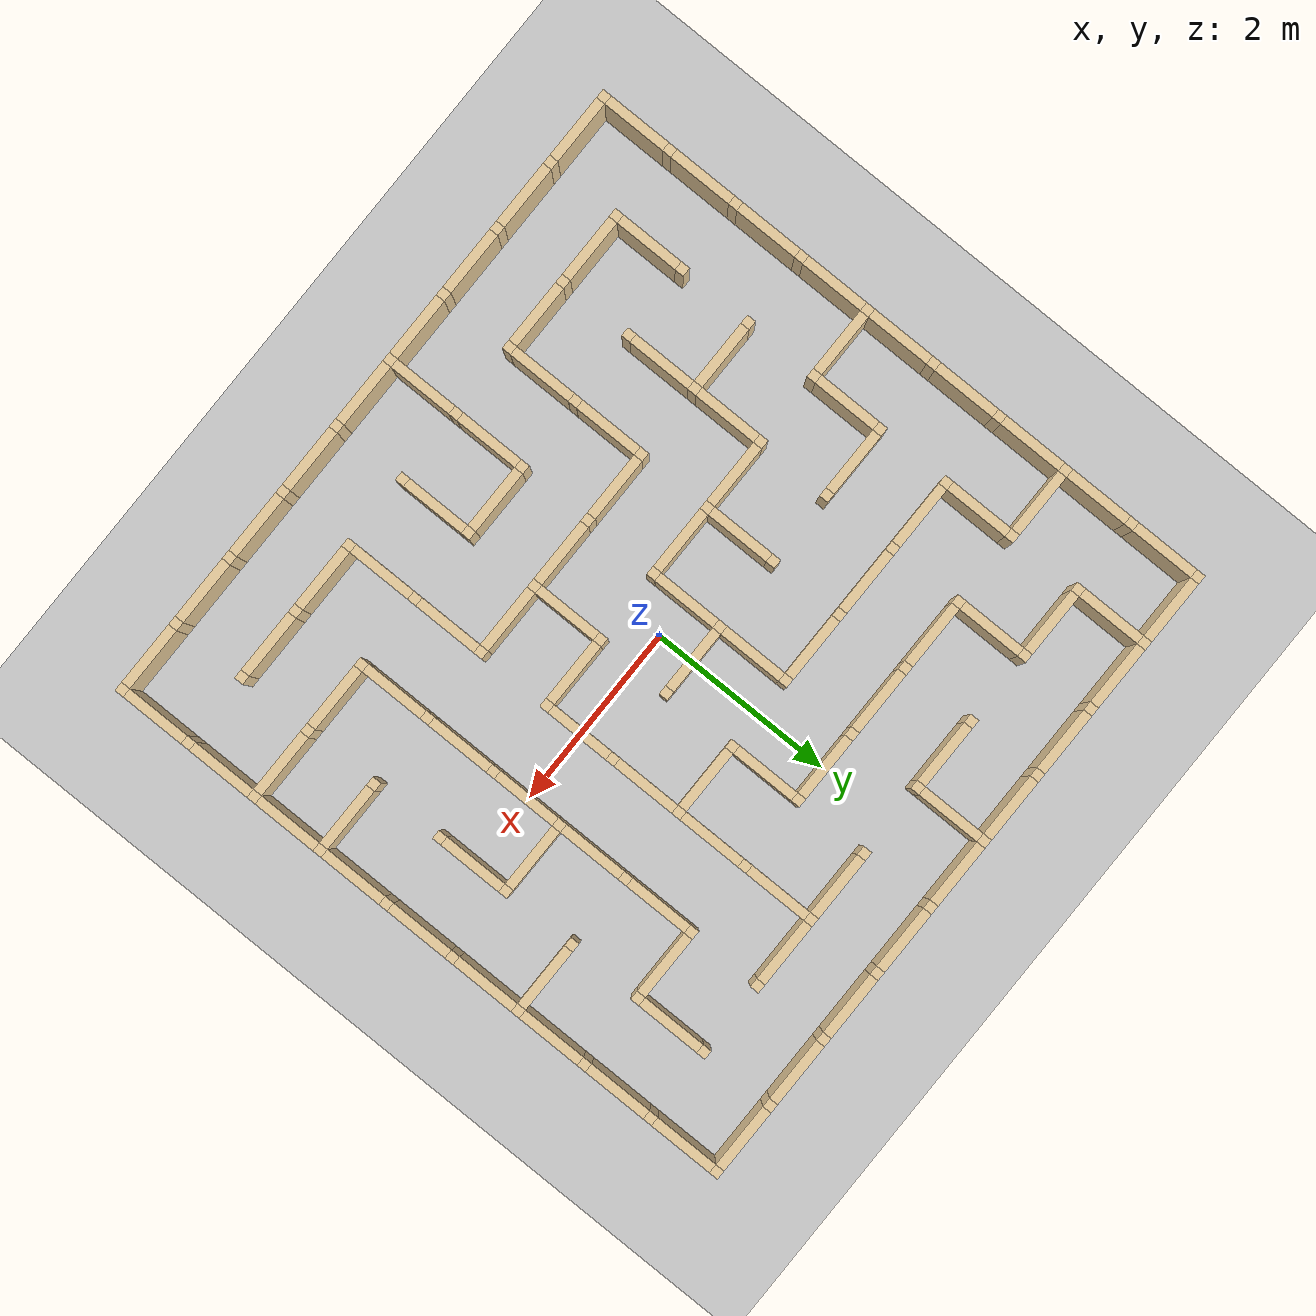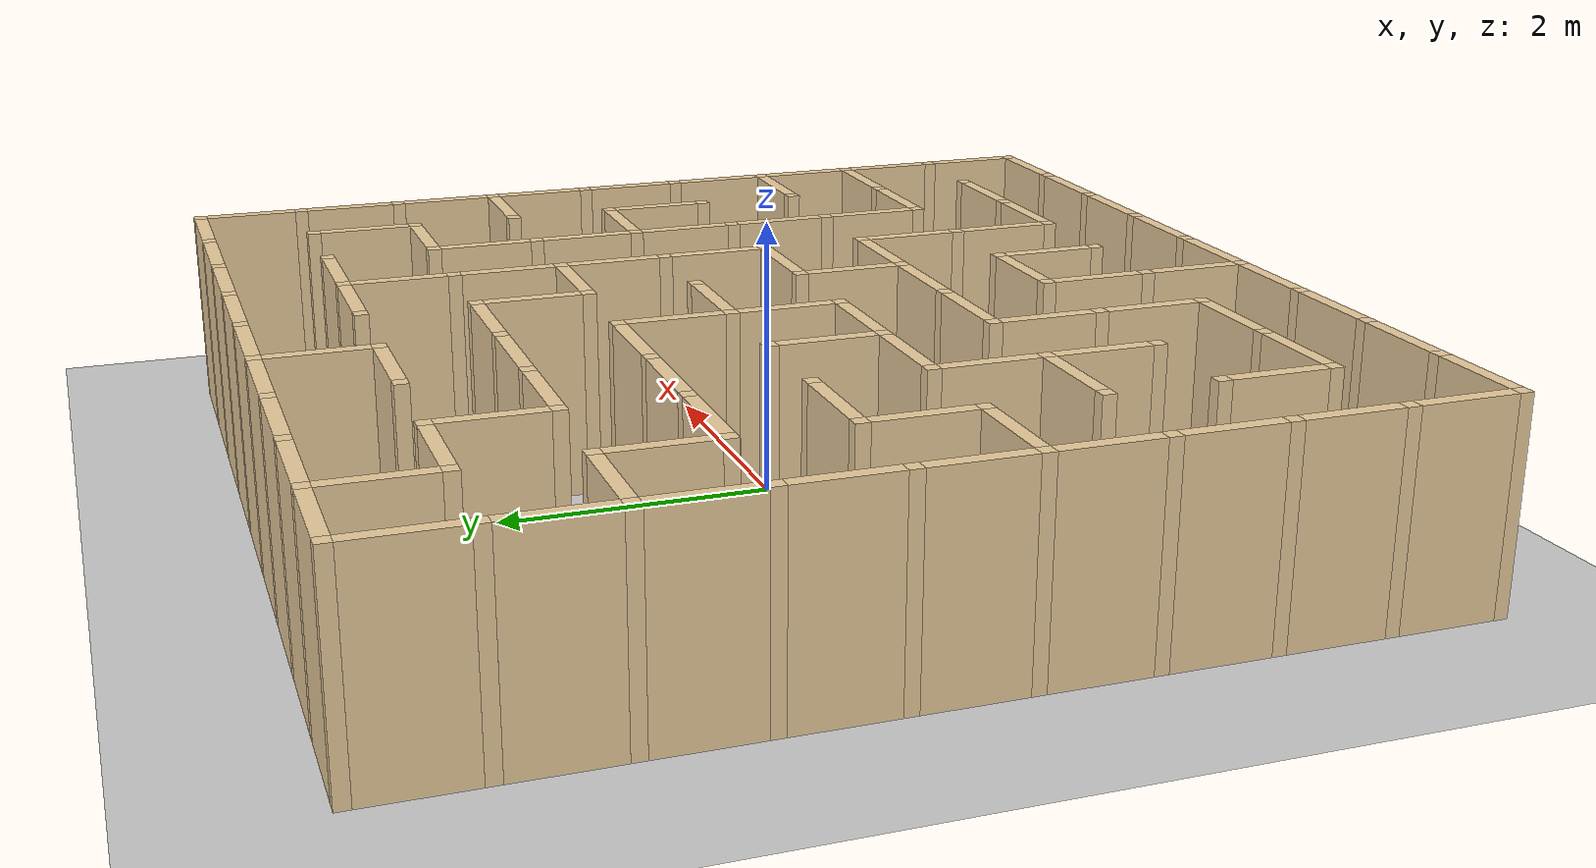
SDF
<?xml version="1.0"?>
<sdf version="1.8">
  <world name="maze_world">

    <plugin
      filename="gz-sim-physics-system"
      name="gz::sim::systems::Physics">
    </plugin>
    <plugin
      filename="gz-sim-user-commands-system"
      name="gz::sim::systems::UserCommands">
    </plugin>
    <plugin
      filename="gz-sim-scene-broadcaster-system"
      name="gz::sim::systems::SceneBroadcaster">
    </plugin>
    <plugin
      filename="gz-sim-sensors-system"
      name="gz::sim::systems::Sensors">
      <render_engine>ogre2</render_engine>
    </plugin>
    <plugin
      filename="gz-sim-imu-system"
      name="gz::sim::systems::Imu">
    </plugin>

    <physics type="ode">
      <real_time_update_rate>1000.0</real_time_update_rate>
      <max_step_size>0.001</max_step_size>
      <real_time_factor>1</real_time_factor>
      <ode>
        <solver>
          <type>quick</type>
          <iters>150</iters>
          <precon_iters>0</precon_iters>
          <sor>1.400000</sor>
          <use_dynamic_moi_rescaling>1</use_dynamic_moi_rescaling>
        </solver>
        <constraints>
          <cfm>0.00001</cfm>
          <erp>0.2</erp>
          <contact_max_correcting_vel>2000.000000</contact_max_correcting_vel>
          <contact_surface_layer>0.01000</contact_surface_layer>
        </constraints>
      </ode>
    </physics>

    <include>
      <uri>https://fuel.gazebosim.org/1.0/OpenRobotics/models/Ground Plane</uri>
    </include>

    <model name="maze">
      <pose>0 0 0 0 0 0</pose>
		  <link name='Wall_0_0_h'>
		    <collision name='Wall_0_Collision'>
		      <geometry>
		        <box>
		          <size>0.7000000000000001 0.1 1.5</size>
		        </box>
		      </geometry>
		      <pose>0 0 0.75 0 -0 0</pose>
		    </collision>
		    <visual name='Wall_0_Visual'>
		      <pose>0 0 0.75 0 -0 0</pose>
		      <geometry>
		        <box>
		          <size>0.7000000000000001 0.1 1.5</size>
		        </box>
		      </geometry>
		      <material>
		        <diffuse>0.921569 0.807843 0.615686 1</diffuse>
		        <ambient>0.921569 0.807843 0.615686 1</ambient>
		      </material>
		      <meta>
		        <layer>0</layer>
		      </meta>
		    </visual>
		    <pose>-3.2 3.6 0 0 -0 0</pose>
		  </link>
        		  <link name='Wall_0_0_v'>
		    <collision name='Wall_0_Collision'>
		      <geometry>
		        <box>
		          <size>0.7000000000000001 0.1 1.5</size>
		        </box>
		      </geometry>
		      <pose>0 0 0.75 0 -0 0</pose>
		    </collision>
		    <visual name='Wall_0_Visual'>
		      <pose>0 0 0.75 0 -0 0</pose>
		      <geometry>
		        <box>
		          <size>0.7000000000000001 0.1 1.5</size>
		        </box>
		      </geometry>
		      <material>
		        <diffuse>0.921569 0.807843 0.615686 1</diffuse>
		        <ambient>0.921569 0.807843 0.615686 1</ambient>
		      </material>
		      <meta>
		        <layer>0</layer>
		      </meta>
		    </visual>
		    <pose>-3.6 3.2 0 0 -0 1.5708</pose>
		  </link>
        	    <link name='Joint_-3.6_3.6'>
		    <collision name='Wall_2_Collision'>
		      <geometry>
		        <box>
		          <size>0.1 0.1 1.5</size>
		        </box>
		      </geometry>
		      <pose>0 0 0.75 0 -0 0</pose>
		    </collision>
		    <visual name='Wall_2_Visual'>
		      <pose>0 0 0.75 0 -0 0</pose>
		      <geometry>
		        <box>
		          <size>0.1 0.1 1.5</size>
		        </box>
		      </geometry>
		      <material>
		        <diffuse>0.921569 0.807843 0.615686 1</diffuse>
		        <ambient>0.721569 0.907843 0.215686 1</ambient>
		      </material>
		      <meta>
		        <layer>0</layer>
		      </meta>
		    </visual>
		    <pose>-3.6 3.6 0 0 -0 0</pose>
		  </link>
        		  <link name='Wall_1_0_h'>
		    <collision name='Wall_0_Collision'>
		      <geometry>
		        <box>
		          <size>0.7000000000000001 0.1 1.5</size>
		        </box>
		      </geometry>
		      <pose>0 0 0.75 0 -0 0</pose>
		    </collision>
		    <visual name='Wall_0_Visual'>
		      <pose>0 0 0.75 0 -0 0</pose>
		      <geometry>
		        <box>
		          <size>0.7000000000000001 0.1 1.5</size>
		        </box>
		      </geometry>
		      <material>
		        <diffuse>0.921569 0.807843 0.615686 1</diffuse>
		        <ambient>0.921569 0.807843 0.615686 1</ambient>
		      </material>
		      <meta>
		        <layer>0</layer>
		      </meta>
		    </visual>
		    <pose>-2.4 3.6 0 0 -0 0</pose>
		  </link>
        		  <link name='Wall_1_0_v'>
		    <collision name='Wall_0_Collision'>
		      <geometry>
		        <box>
		          <size>0.7000000000000001 0.1 1.5</size>
		        </box>
		      </geometry>
		      <pose>0 0 0.75 0 -0 0</pose>
		    </collision>
		    <visual name='Wall_0_Visual'>
		      <pose>0 0 0.75 0 -0 0</pose>
		      <geometry>
		        <box>
		          <size>0.7000000000000001 0.1 1.5</size>
		        </box>
		      </geometry>
		      <material>
		        <diffuse>0.921569 0.807843 0.615686 1</diffuse>
		        <ambient>0.921569 0.807843 0.615686 1</ambient>
		      </material>
		      <meta>
		        <layer>0</layer>
		      </meta>
		    </visual>
		    <pose>-2.8 3.2 0 0 -0 1.5708</pose>
		  </link>
        	    <link name='Joint_-2.8_3.6'>
		    <collision name='Wall_2_Collision'>
		      <geometry>
		        <box>
		          <size>0.1 0.1 1.5</size>
		        </box>
		      </geometry>
		      <pose>0 0 0.75 0 -0 0</pose>
		    </collision>
		    <visual name='Wall_2_Visual'>
		      <pose>0 0 0.75 0 -0 0</pose>
		      <geometry>
		        <box>
		          <size>0.1 0.1 1.5</size>
		        </box>
		      </geometry>
		      <material>
		        <diffuse>0.921569 0.807843 0.615686 1</diffuse>
		        <ambient>0.721569 0.907843 0.215686 1</ambient>
		      </material>
		      <meta>
		        <layer>0</layer>
		      </meta>
		    </visual>
		    <pose>-2.8 3.6 0 0 -0 0</pose>
		  </link>
        		  <link name='Wall_2_0_h'>
		    <collision name='Wall_0_Collision'>
		      <geometry>
		        <box>
		          <size>0.7000000000000001 0.1 1.5</size>
		        </box>
		      </geometry>
		      <pose>0 0 0.75 0 -0 0</pose>
		    </collision>
		    <visual name='Wall_0_Visual'>
		      <pose>0 0 0.75 0 -0 0</pose>
		      <geometry>
		        <box>
		          <size>0.7000000000000001 0.1 1.5</size>
		        </box>
		      </geometry>
		      <material>
		        <diffuse>0.921569 0.807843 0.615686 1</diffuse>
		        <ambient>0.921569 0.807843 0.615686 1</ambient>
		      </material>
		      <meta>
		        <layer>0</layer>
		      </meta>
		    </visual>
		    <pose>-1.6 3.6 0 0 -0 0</pose>
		  </link>
        	    <link name='Joint_-2.0_3.6'>
		    <collision name='Wall_2_Collision'>
		      <geometry>
		        <box>
		          <size>0.1 0.1 1.5</size>
		        </box>
		      </geometry>
		      <pose>0 0 0.75 0 -0 0</pose>
		    </collision>
		    <visual name='Wall_2_Visual'>
		      <pose>0 0 0.75 0 -0 0</pose>
		      <geometry>
		        <box>
		          <size>0.1 0.1 1.5</size>
		        </box>
		      </geometry>
		      <material>
		        <diffuse>0.921569 0.807843 0.615686 1</diffuse>
		        <ambient>0.721569 0.907843 0.215686 1</ambient>
		      </material>
		      <meta>
		        <layer>0</layer>
		      </meta>
		    </visual>
		    <pose>-2.0 3.6 0 0 -0 0</pose>
		  </link>
        		  <link name='Wall_3_0_h'>
		    <collision name='Wall_0_Collision'>
		      <geometry>
		        <box>
		          <size>0.7000000000000001 0.1 1.5</size>
		        </box>
		      </geometry>
		      <pose>0 0 0.75 0 -0 0</pose>
		    </collision>
		    <visual name='Wall_0_Visual'>
		      <pose>0 0 0.75 0 -0 0</pose>
		      <geometry>
		        <box>
		          <size>0.7000000000000001 0.1 1.5</size>
		        </box>
		      </geometry>
		      <material>
		        <diffuse>0.921569 0.807843 0.615686 1</diffuse>
		        <ambient>0.921569 0.807843 0.615686 1</ambient>
		      </material>
		      <meta>
		        <layer>0</layer>
		      </meta>
		    </visual>
		    <pose>-0.7999999999999998 3.6 0 0 -0 0</pose>
		  </link>
        	    <link name='Joint_-1.1999999999999997_3.6'>
		    <collision name='Wall_2_Collision'>
		      <geometry>
		        <box>
		          <size>0.1 0.1 1.5</size>
		        </box>
		      </geometry>
		      <pose>0 0 0.75 0 -0 0</pose>
		    </collision>
		    <visual name='Wall_2_Visual'>
		      <pose>0 0 0.75 0 -0 0</pose>
		      <geometry>
		        <box>
		          <size>0.1 0.1 1.5</size>
		        </box>
		      </geometry>
		      <material>
		        <diffuse>0.921569 0.807843 0.615686 1</diffuse>
		        <ambient>0.721569 0.907843 0.215686 1</ambient>
		      </material>
		      <meta>
		        <layer>0</layer>
		      </meta>
		    </visual>
		    <pose>-1.1999999999999997 3.6 0 0 -0 0</pose>
		  </link>
        		  <link name='Wall_4_0_h'>
		    <collision name='Wall_0_Collision'>
		      <geometry>
		        <box>
		          <size>0.7000000000000001 0.1 1.5</size>
		        </box>
		      </geometry>
		      <pose>0 0 0.75 0 -0 0</pose>
		    </collision>
		    <visual name='Wall_0_Visual'>
		      <pose>0 0 0.75 0 -0 0</pose>
		      <geometry>
		        <box>
		          <size>0.7000000000000001 0.1 1.5</size>
		        </box>
		      </geometry>
		      <material>
		        <diffuse>0.921569 0.807843 0.615686 1</diffuse>
		        <ambient>0.921569 0.807843 0.615686 1</ambient>
		      </material>
		      <meta>
		        <layer>0</layer>
		      </meta>
		    </visual>
		    <pose>0.0 3.6 0 0 -0 0</pose>
		  </link>
        		  <link name='Wall_4_0_v'>
		    <collision name='Wall_0_Collision'>
		      <geometry>
		        <box>
		          <size>0.7000000000000001 0.1 1.5</size>
		        </box>
		      </geometry>
		      <pose>0 0 0.75 0 -0 0</pose>
		    </collision>
		    <visual name='Wall_0_Visual'>
		      <pose>0 0 0.75 0 -0 0</pose>
		      <geometry>
		        <box>
		          <size>0.7000000000000001 0.1 1.5</size>
		        </box>
		      </geometry>
		      <material>
		        <diffuse>0.921569 0.807843 0.615686 1</diffuse>
		        <ambient>0.921569 0.807843 0.615686 1</ambient>
		      </material>
		      <meta>
		        <layer>0</layer>
		      </meta>
		    </visual>
		    <pose>-0.3999999999999999 3.2 0 0 -0 1.5708</pose>
		  </link>
        	    <link name='Joint_-0.3999999999999999_3.6'>
		    <collision name='Wall_2_Collision'>
		      <geometry>
		        <box>
		          <size>0.1 0.1 1.5</size>
		        </box>
		      </geometry>
		      <pose>0 0 0.75 0 -0 0</pose>
		    </collision>
		    <visual name='Wall_2_Visual'>
		      <pose>0 0 0.75 0 -0 0</pose>
		      <geometry>
		        <box>
		          <size>0.1 0.1 1.5</size>
		        </box>
		      </geometry>
		      <material>
		        <diffuse>0.921569 0.807843 0.615686 1</diffuse>
		        <ambient>0.721569 0.907843 0.215686 1</ambient>
		      </material>
		      <meta>
		        <layer>0</layer>
		      </meta>
		    </visual>
		    <pose>-0.3999999999999999 3.6 0 0 -0 0</pose>
		  </link>
        		  <link name='Wall_5_0_h'>
		    <collision name='Wall_0_Collision'>
		      <geometry>
		        <box>
		          <size>0.7000000000000001 0.1 1.5</size>
		        </box>
		      </geometry>
		      <pose>0 0 0.75 0 -0 0</pose>
		    </collision>
		    <visual name='Wall_0_Visual'>
		      <pose>0 0 0.75 0 -0 0</pose>
		      <geometry>
		        <box>
		          <size>0.7000000000000001 0.1 1.5</size>
		        </box>
		      </geometry>
		      <material>
		        <diffuse>0.921569 0.807843 0.615686 1</diffuse>
		        <ambient>0.921569 0.807843 0.615686 1</ambient>
		      </material>
		      <meta>
		        <layer>0</layer>
		      </meta>
		    </visual>
		    <pose>0.8000000000000003 3.6 0 0 -0 0</pose>
		  </link>
        	    <link name='Joint_0.3999999999999999_3.6'>
		    <collision name='Wall_2_Collision'>
		      <geometry>
		        <box>
		          <size>0.1 0.1 1.5</size>
		        </box>
		      </geometry>
		      <pose>0 0 0.75 0 -0 0</pose>
		    </collision>
		    <visual name='Wall_2_Visual'>
		      <pose>0 0 0.75 0 -0 0</pose>
		      <geometry>
		        <box>
		          <size>0.1 0.1 1.5</size>
		        </box>
		      </geometry>
		      <material>
		        <diffuse>0.921569 0.807843 0.615686 1</diffuse>
		        <ambient>0.721569 0.907843 0.215686 1</ambient>
		      </material>
		      <meta>
		        <layer>0</layer>
		      </meta>
		    </visual>
		    <pose>0.3999999999999999 3.6 0 0 -0 0</pose>
		  </link>
        		  <link name='Wall_6_0_h'>
		    <collision name='Wall_0_Collision'>
		      <geometry>
		        <box>
		          <size>0.7000000000000001 0.1 1.5</size>
		        </box>
		      </geometry>
		      <pose>0 0 0.75 0 -0 0</pose>
		    </collision>
		    <visual name='Wall_0_Visual'>
		      <pose>0 0 0.75 0 -0 0</pose>
		      <geometry>
		        <box>
		          <size>0.7000000000000001 0.1 1.5</size>
		        </box>
		      </geometry>
		      <material>
		        <diffuse>0.921569 0.807843 0.615686 1</diffuse>
		        <ambient>0.921569 0.807843 0.615686 1</ambient>
		      </material>
		      <meta>
		        <layer>0</layer>
		      </meta>
		    </visual>
		    <pose>1.600000000000001 3.6 0 0 -0 0</pose>
		  </link>
        	    <link name='Joint_1.2000000000000006_3.6'>
		    <collision name='Wall_2_Collision'>
		      <geometry>
		        <box>
		          <size>0.1 0.1 1.5</size>
		        </box>
		      </geometry>
		      <pose>0 0 0.75 0 -0 0</pose>
		    </collision>
		    <visual name='Wall_2_Visual'>
		      <pose>0 0 0.75 0 -0 0</pose>
		      <geometry>
		        <box>
		          <size>0.1 0.1 1.5</size>
		        </box>
		      </geometry>
		      <material>
		        <diffuse>0.921569 0.807843 0.615686 1</diffuse>
		        <ambient>0.721569 0.907843 0.215686 1</ambient>
		      </material>
		      <meta>
		        <layer>0</layer>
		      </meta>
		    </visual>
		    <pose>1.2000000000000006 3.6 0 0 -0 0</pose>
		  </link>
        		  <link name='Wall_7_0_h'>
		    <collision name='Wall_0_Collision'>
		      <geometry>
		        <box>
		          <size>0.7000000000000001 0.1 1.5</size>
		        </box>
		      </geometry>
		      <pose>0 0 0.75 0 -0 0</pose>
		    </collision>
		    <visual name='Wall_0_Visual'>
		      <pose>0 0 0.75 0 -0 0</pose>
		      <geometry>
		        <box>
		          <size>0.7000000000000001 0.1 1.5</size>
		        </box>
		      </geometry>
		      <material>
		        <diffuse>0.921569 0.807843 0.615686 1</diffuse>
		        <ambient>0.921569 0.807843 0.615686 1</ambient>
		      </material>
		      <meta>
		        <layer>0</layer>
		      </meta>
		    </visual>
		    <pose>2.400000000000001 3.6 0 0 -0 0</pose>
		  </link>
        	    <link name='Joint_2.0000000000000004_3.6'>
		    <collision name='Wall_2_Collision'>
		      <geometry>
		        <box>
		          <size>0.1 0.1 1.5</size>
		        </box>
		      </geometry>
		      <pose>0 0 0.75 0 -0 0</pose>
		    </collision>
		    <visual name='Wall_2_Visual'>
		      <pose>0 0 0.75 0 -0 0</pose>
		      <geometry>
		        <box>
		          <size>0.1 0.1 1.5</size>
		        </box>
		      </geometry>
		      <material>
		        <diffuse>0.921569 0.807843 0.615686 1</diffuse>
		        <ambient>0.721569 0.907843 0.215686 1</ambient>
		      </material>
		      <meta>
		        <layer>0</layer>
		      </meta>
		    </visual>
		    <pose>2.0000000000000004 3.6 0 0 -0 0</pose>
		  </link>
        		  <link name='Wall_8_0_h'>
		    <collision name='Wall_0_Collision'>
		      <geometry>
		        <box>
		          <size>0.7000000000000001 0.1 1.5</size>
		        </box>
		      </geometry>
		      <pose>0 0 0.75 0 -0 0</pose>
		    </collision>
		    <visual name='Wall_0_Visual'>
		      <pose>0 0 0.75 0 -0 0</pose>
		      <geometry>
		        <box>
		          <size>0.7000000000000001 0.1 1.5</size>
		        </box>
		      </geometry>
		      <material>
		        <diffuse>0.921569 0.807843 0.615686 1</diffuse>
		        <ambient>0.921569 0.807843 0.615686 1</ambient>
		      </material>
		      <meta>
		        <layer>0</layer>
		      </meta>
		    </visual>
		    <pose>3.2000000000000006 3.6 0 0 -0 0</pose>
		  </link>
        	    <link name='Joint_2.8000000000000003_3.6'>
		    <collision name='Wall_2_Collision'>
		      <geometry>
		        <box>
		          <size>0.1 0.1 1.5</size>
		        </box>
		      </geometry>
		      <pose>0 0 0.75 0 -0 0</pose>
		    </collision>
		    <visual name='Wall_2_Visual'>
		      <pose>0 0 0.75 0 -0 0</pose>
		      <geometry>
		        <box>
		          <size>0.1 0.1 1.5</size>
		        </box>
		      </geometry>
		      <material>
		        <diffuse>0.921569 0.807843 0.615686 1</diffuse>
		        <ambient>0.721569 0.907843 0.215686 1</ambient>
		      </material>
		      <meta>
		        <layer>0</layer>
		      </meta>
		    </visual>
		    <pose>2.8000000000000003 3.6 0 0 -0 0</pose>
		  </link>
        		  <link name='Wall_9_0_v'>
		    <collision name='Wall_0_Collision'>
		      <geometry>
		        <box>
		          <size>0.7000000000000001 0.1 1.5</size>
		        </box>
		      </geometry>
		      <pose>0 0 0.75 0 -0 0</pose>
		    </collision>
		    <visual name='Wall_0_Visual'>
		      <pose>0 0 0.75 0 -0 0</pose>
		      <geometry>
		        <box>
		          <size>0.7000000000000001 0.1 1.5</size>
		        </box>
		      </geometry>
		      <material>
		        <diffuse>0.921569 0.807843 0.615686 1</diffuse>
		        <ambient>0.921569 0.807843 0.615686 1</ambient>
		      </material>
		      <meta>
		        <layer>0</layer>
		      </meta>
		    </visual>
		    <pose>3.6 3.2 0 0 -0 1.5708</pose>
		  </link>
        	    <link name='Joint_3.6_3.6'>
		    <collision name='Wall_2_Collision'>
		      <geometry>
		        <box>
		          <size>0.1 0.1 1.5</size>
		        </box>
		      </geometry>
		      <pose>0 0 0.75 0 -0 0</pose>
		    </collision>
		    <visual name='Wall_2_Visual'>
		      <pose>0 0 0.75 0 -0 0</pose>
		      <geometry>
		        <box>
		          <size>0.1 0.1 1.5</size>
		        </box>
		      </geometry>
		      <material>
		        <diffuse>0.921569 0.807843 0.615686 1</diffuse>
		        <ambient>0.721569 0.907843 0.215686 1</ambient>
		      </material>
		      <meta>
		        <layer>0</layer>
		      </meta>
		    </visual>
		    <pose>3.6 3.6 0 0 -0 0</pose>
		  </link>
        		  <link name='Wall_0_1_v'>
		    <collision name='Wall_0_Collision'>
		      <geometry>
		        <box>
		          <size>0.7000000000000001 0.1 1.5</size>
		        </box>
		      </geometry>
		      <pose>0 0 0.75 0 -0 0</pose>
		    </collision>
		    <visual name='Wall_0_Visual'>
		      <pose>0 0 0.75 0 -0 0</pose>
		      <geometry>
		        <box>
		          <size>0.7000000000000001 0.1 1.5</size>
		        </box>
		      </geometry>
		      <material>
		        <diffuse>0.921569 0.807843 0.615686 1</diffuse>
		        <ambient>0.921569 0.807843 0.615686 1</ambient>
		      </material>
		      <meta>
		        <layer>0</layer>
		      </meta>
		    </visual>
		    <pose>-3.6 2.4 0 0 -0 1.5708</pose>
		  </link>
        	    <link name='Joint_-3.6_2.8'>
		    <collision name='Wall_2_Collision'>
		      <geometry>
		        <box>
		          <size>0.1 0.1 1.5</size>
		        </box>
		      </geometry>
		      <pose>0 0 0.75 0 -0 0</pose>
		    </collision>
		    <visual name='Wall_2_Visual'>
		      <pose>0 0 0.75 0 -0 0</pose>
		      <geometry>
		        <box>
		          <size>0.1 0.1 1.5</size>
		        </box>
		      </geometry>
		      <material>
		        <diffuse>0.921569 0.807843 0.615686 1</diffuse>
		        <ambient>0.721569 0.907843 0.215686 1</ambient>
		      </material>
		      <meta>
		        <layer>0</layer>
		      </meta>
		    </visual>
		    <pose>-3.6 2.8 0 0 -0 0</pose>
		  </link>
        		  <link name='Wall_1_1_h'>
		    <collision name='Wall_0_Collision'>
		      <geometry>
		        <box>
		          <size>0.7000000000000001 0.1 1.5</size>
		        </box>
		      </geometry>
		      <pose>0 0 0.75 0 -0 0</pose>
		    </collision>
		    <visual name='Wall_0_Visual'>
		      <pose>0 0 0.75 0 -0 0</pose>
		      <geometry>
		        <box>
		          <size>0.7000000000000001 0.1 1.5</size>
		        </box>
		      </geometry>
		      <material>
		        <diffuse>0.921569 0.807843 0.615686 1</diffuse>
		        <ambient>0.921569 0.807843 0.615686 1</ambient>
		      </material>
		      <meta>
		        <layer>0</layer>
		      </meta>
		    </visual>
		    <pose>-2.4 2.8 0 0 -0 0</pose>
		  </link>
        	    <link name='Joint_-2.8_2.8'>
		    <collision name='Wall_2_Collision'>
		      <geometry>
		        <box>
		          <size>0.1 0.1 1.5</size>
		        </box>
		      </geometry>
		      <pose>0 0 0.75 0 -0 0</pose>
		    </collision>
		    <visual name='Wall_2_Visual'>
		      <pose>0 0 0.75 0 -0 0</pose>
		      <geometry>
		        <box>
		          <size>0.1 0.1 1.5</size>
		        </box>
		      </geometry>
		      <material>
		        <diffuse>0.921569 0.807843 0.615686 1</diffuse>
		        <ambient>0.721569 0.907843 0.215686 1</ambient>
		      </material>
		      <meta>
		        <layer>0</layer>
		      </meta>
		    </visual>
		    <pose>-2.8 2.8 0 0 -0 0</pose>
		  </link>
        		  <link name='Wall_2_1_v'>
		    <collision name='Wall_0_Collision'>
		      <geometry>
		        <box>
		          <size>0.7000000000000001 0.1 1.5</size>
		        </box>
		      </geometry>
		      <pose>0 0 0.75 0 -0 0</pose>
		    </collision>
		    <visual name='Wall_0_Visual'>
		      <pose>0 0 0.75 0 -0 0</pose>
		      <geometry>
		        <box>
		          <size>0.7000000000000001 0.1 1.5</size>
		        </box>
		      </geometry>
		      <material>
		        <diffuse>0.921569 0.807843 0.615686 1</diffuse>
		        <ambient>0.921569 0.807843 0.615686 1</ambient>
		      </material>
		      <meta>
		        <layer>0</layer>
		      </meta>
		    </visual>
		    <pose>-2.0 2.4 0 0 -0 1.5708</pose>
		  </link>
        	    <link name='Joint_-2.0_2.8'>
		    <collision name='Wall_2_Collision'>
		      <geometry>
		        <box>
		          <size>0.1 0.1 1.5</size>
		        </box>
		      </geometry>
		      <pose>0 0 0.75 0 -0 0</pose>
		    </collision>
		    <visual name='Wall_2_Visual'>
		      <pose>0 0 0.75 0 -0 0</pose>
		      <geometry>
		        <box>
		          <size>0.1 0.1 1.5</size>
		        </box>
		      </geometry>
		      <material>
		        <diffuse>0.921569 0.807843 0.615686 1</diffuse>
		        <ambient>0.721569 0.907843 0.215686 1</ambient>
		      </material>
		      <meta>
		        <layer>0</layer>
		      </meta>
		    </visual>
		    <pose>-2.0 2.8 0 0 -0 0</pose>
		  </link>
        		  <link name='Wall_3_1_h'>
		    <collision name='Wall_0_Collision'>
		      <geometry>
		        <box>
		          <size>0.7000000000000001 0.1 1.5</size>
		        </box>
		      </geometry>
		      <pose>0 0 0.75 0 -0 0</pose>
		    </collision>
		    <visual name='Wall_0_Visual'>
		      <pose>0 0 0.75 0 -0 0</pose>
		      <geometry>
		        <box>
		          <size>0.7000000000000001 0.1 1.5</size>
		        </box>
		      </geometry>
		      <material>
		        <diffuse>0.921569 0.807843 0.615686 1</diffuse>
		        <ambient>0.921569 0.807843 0.615686 1</ambient>
		      </material>
		      <meta>
		        <layer>0</layer>
		      </meta>
		    </visual>
		    <pose>-0.7999999999999998 2.8 0 0 -0 0</pose>
		  </link>
        	    <link name='Joint_-1.1999999999999997_2.8'>
		    <collision name='Wall_2_Collision'>
		      <geometry>
		        <box>
		          <size>0.1 0.1 1.5</size>
		        </box>
		      </geometry>
		      <pose>0 0 0.75 0 -0 0</pose>
		    </collision>
		    <visual name='Wall_2_Visual'>
		      <pose>0 0 0.75 0 -0 0</pose>
		      <geometry>
		        <box>
		          <size>0.1 0.1 1.5</size>
		        </box>
		      </geometry>
		      <material>
		        <diffuse>0.921569 0.807843 0.615686 1</diffuse>
		        <ambient>0.721569 0.907843 0.215686 1</ambient>
		      </material>
		      <meta>
		        <layer>0</layer>
		      </meta>
		    </visual>
		    <pose>-1.1999999999999997 2.8 0 0 -0 0</pose>
		  </link>
        	    <link name='Joint_-0.3999999999999999_2.8'>
		    <collision name='Wall_2_Collision'>
		      <geometry>
		        <box>
		          <size>0.1 0.1 1.5</size>
		        </box>
		      </geometry>
		      <pose>0 0 0.75 0 -0 0</pose>
		    </collision>
		    <visual name='Wall_2_Visual'>
		      <pose>0 0 0.75 0 -0 0</pose>
		      <geometry>
		        <box>
		          <size>0.1 0.1 1.5</size>
		        </box>
		      </geometry>
		      <material>
		        <diffuse>0.921569 0.807843 0.615686 1</diffuse>
		        <ambient>0.721569 0.907843 0.215686 1</ambient>
		      </material>
		      <meta>
		        <layer>0</layer>
		      </meta>
		    </visual>
		    <pose>-0.3999999999999999 2.8 0 0 -0 0</pose>
		  </link>
        		  <link name='Wall_5_1_h'>
		    <collision name='Wall_0_Collision'>
		      <geometry>
		        <box>
		          <size>0.7000000000000001 0.1 1.5</size>
		        </box>
		      </geometry>
		      <pose>0 0 0.75 0 -0 0</pose>
		    </collision>
		    <visual name='Wall_0_Visual'>
		      <pose>0 0 0.75 0 -0 0</pose>
		      <geometry>
		        <box>
		          <size>0.7000000000000001 0.1 1.5</size>
		        </box>
		      </geometry>
		      <material>
		        <diffuse>0.921569 0.807843 0.615686 1</diffuse>
		        <ambient>0.921569 0.807843 0.615686 1</ambient>
		      </material>
		      <meta>
		        <layer>0</layer>
		      </meta>
		    </visual>
		    <pose>0.8000000000000003 2.8 0 0 -0 0</pose>
		  </link>
        	    <link name='Joint_0.3999999999999999_2.8'>
		    <collision name='Wall_2_Collision'>
		      <geometry>
		        <box>
		          <size>0.1 0.1 1.5</size>
		        </box>
		      </geometry>
		      <pose>0 0 0.75 0 -0 0</pose>
		    </collision>
		    <visual name='Wall_2_Visual'>
		      <pose>0 0 0.75 0 -0 0</pose>
		      <geometry>
		        <box>
		          <size>0.1 0.1 1.5</size>
		        </box>
		      </geometry>
		      <material>
		        <diffuse>0.921569 0.807843 0.615686 1</diffuse>
		        <ambient>0.721569 0.907843 0.215686 1</ambient>
		      </material>
		      <meta>
		        <layer>0</layer>
		      </meta>
		    </visual>
		    <pose>0.3999999999999999 2.8 0 0 -0 0</pose>
		  </link>
        		  <link name='Wall_6_1_h'>
		    <collision name='Wall_0_Collision'>
		      <geometry>
		        <box>
		          <size>0.7000000000000001 0.1 1.5</size>
		        </box>
		      </geometry>
		      <pose>0 0 0.75 0 -0 0</pose>
		    </collision>
		    <visual name='Wall_0_Visual'>
		      <pose>0 0 0.75 0 -0 0</pose>
		      <geometry>
		        <box>
		          <size>0.7000000000000001 0.1 1.5</size>
		        </box>
		      </geometry>
		      <material>
		        <diffuse>0.921569 0.807843 0.615686 1</diffuse>
		        <ambient>0.921569 0.807843 0.615686 1</ambient>
		      </material>
		      <meta>
		        <layer>0</layer>
		      </meta>
		    </visual>
		    <pose>1.600000000000001 2.8 0 0 -0 0</pose>
		  </link>
        		  <link name='Wall_6_1_v'>
		    <collision name='Wall_0_Collision'>
		      <geometry>
		        <box>
		          <size>0.7000000000000001 0.1 1.5</size>
		        </box>
		      </geometry>
		      <pose>0 0 0.75 0 -0 0</pose>
		    </collision>
		    <visual name='Wall_0_Visual'>
		      <pose>0 0 0.75 0 -0 0</pose>
		      <geometry>
		        <box>
		          <size>0.7000000000000001 0.1 1.5</size>
		        </box>
		      </geometry>
		      <material>
		        <diffuse>0.921569 0.807843 0.615686 1</diffuse>
		        <ambient>0.921569 0.807843 0.615686 1</ambient>
		      </material>
		      <meta>
		        <layer>0</layer>
		      </meta>
		    </visual>
		    <pose>1.2000000000000006 2.4 0 0 -0 1.5708</pose>
		  </link>
        	    <link name='Joint_1.2000000000000006_2.8'>
		    <collision name='Wall_2_Collision'>
		      <geometry>
		        <box>
		          <size>0.1 0.1 1.5</size>
		        </box>
		      </geometry>
		      <pose>0 0 0.75 0 -0 0</pose>
		    </collision>
		    <visual name='Wall_2_Visual'>
		      <pose>0 0 0.75 0 -0 0</pose>
		      <geometry>
		        <box>
		          <size>0.1 0.1 1.5</size>
		        </box>
		      </geometry>
		      <material>
		        <diffuse>0.921569 0.807843 0.615686 1</diffuse>
		        <ambient>0.721569 0.907843 0.215686 1</ambient>
		      </material>
		      <meta>
		        <layer>0</layer>
		      </meta>
		    </visual>
		    <pose>1.2000000000000006 2.8 0 0 -0 0</pose>
		  </link>
        	    <link name='Joint_2.0000000000000004_2.8'>
		    <collision name='Wall_2_Collision'>
		      <geometry>
		        <box>
		          <size>0.1 0.1 1.5</size>
		        </box>
		      </geometry>
		      <pose>0 0 0.75 0 -0 0</pose>
		    </collision>
		    <visual name='Wall_2_Visual'>
		      <pose>0 0 0.75 0 -0 0</pose>
		      <geometry>
		        <box>
		          <size>0.1 0.1 1.5</size>
		        </box>
		      </geometry>
		      <material>
		        <diffuse>0.921569 0.807843 0.615686 1</diffuse>
		        <ambient>0.721569 0.907843 0.215686 1</ambient>
		      </material>
		      <meta>
		        <layer>0</layer>
		      </meta>
		    </visual>
		    <pose>2.0000000000000004 2.8 0 0 -0 0</pose>
		  </link>
        		  <link name='Wall_8_1_v'>
		    <collision name='Wall_0_Collision'>
		      <geometry>
		        <box>
		          <size>0.7000000000000001 0.1 1.5</size>
		        </box>
		      </geometry>
		      <pose>0 0 0.75 0 -0 0</pose>
		    </collision>
		    <visual name='Wall_0_Visual'>
		      <pose>0 0 0.75 0 -0 0</pose>
		      <geometry>
		        <box>
		          <size>0.7000000000000001 0.1 1.5</size>
		        </box>
		      </geometry>
		      <material>
		        <diffuse>0.921569 0.807843 0.615686 1</diffuse>
		        <ambient>0.921569 0.807843 0.615686 1</ambient>
		      </material>
		      <meta>
		        <layer>0</layer>
		      </meta>
		    </visual>
		    <pose>2.8000000000000003 2.4 0 0 -0 1.5708</pose>
		  </link>
        	    <link name='Joint_2.8000000000000003_2.8'>
		    <collision name='Wall_2_Collision'>
		      <geometry>
		        <box>
		          <size>0.1 0.1 1.5</size>
		        </box>
		      </geometry>
		      <pose>0 0 0.75 0 -0 0</pose>
		    </collision>
		    <visual name='Wall_2_Visual'>
		      <pose>0 0 0.75 0 -0 0</pose>
		      <geometry>
		        <box>
		          <size>0.1 0.1 1.5</size>
		        </box>
		      </geometry>
		      <material>
		        <diffuse>0.921569 0.807843 0.615686 1</diffuse>
		        <ambient>0.721569 0.907843 0.215686 1</ambient>
		      </material>
		      <meta>
		        <layer>0</layer>
		      </meta>
		    </visual>
		    <pose>2.8000000000000003 2.8 0 0 -0 0</pose>
		  </link>
        		  <link name='Wall_9_1_v'>
		    <collision name='Wall_0_Collision'>
		      <geometry>
		        <box>
		          <size>0.7000000000000001 0.1 1.5</size>
		        </box>
		      </geometry>
		      <pose>0 0 0.75 0 -0 0</pose>
		    </collision>
		    <visual name='Wall_0_Visual'>
		      <pose>0 0 0.75 0 -0 0</pose>
		      <geometry>
		        <box>
		          <size>0.7000000000000001 0.1 1.5</size>
		        </box>
		      </geometry>
		      <material>
		        <diffuse>0.921569 0.807843 0.615686 1</diffuse>
		        <ambient>0.921569 0.807843 0.615686 1</ambient>
		      </material>
		      <meta>
		        <layer>0</layer>
		      </meta>
		    </visual>
		    <pose>3.6 2.4 0 0 -0 1.5708</pose>
		  </link>
        	    <link name='Joint_3.6_2.8'>
		    <collision name='Wall_2_Collision'>
		      <geometry>
		        <box>
		          <size>0.1 0.1 1.5</size>
		        </box>
		      </geometry>
		      <pose>0 0 0.75 0 -0 0</pose>
		    </collision>
		    <visual name='Wall_2_Visual'>
		      <pose>0 0 0.75 0 -0 0</pose>
		      <geometry>
		        <box>
		          <size>0.1 0.1 1.5</size>
		        </box>
		      </geometry>
		      <material>
		        <diffuse>0.921569 0.807843 0.615686 1</diffuse>
		        <ambient>0.721569 0.907843 0.215686 1</ambient>
		      </material>
		      <meta>
		        <layer>0</layer>
		      </meta>
		    </visual>
		    <pose>3.6 2.8 0 0 -0 0</pose>
		  </link>
        		  <link name='Wall_0_2_h'>
		    <collision name='Wall_0_Collision'>
		      <geometry>
		        <box>
		          <size>0.7000000000000001 0.1 1.5</size>
		        </box>
		      </geometry>
		      <pose>0 0 0.75 0 -0 0</pose>
		    </collision>
		    <visual name='Wall_0_Visual'>
		      <pose>0 0 0.75 0 -0 0</pose>
		      <geometry>
		        <box>
		          <size>0.7000000000000001 0.1 1.5</size>
		        </box>
		      </geometry>
		      <material>
		        <diffuse>0.921569 0.807843 0.615686 1</diffuse>
		        <ambient>0.921569 0.807843 0.615686 1</ambient>
		      </material>
		      <meta>
		        <layer>0</layer>
		      </meta>
		    </visual>
		    <pose>-3.2 2.0 0 0 -0 0</pose>
		  </link>
        		  <link name='Wall_0_2_v'>
		    <collision name='Wall_0_Collision'>
		      <geometry>
		        <box>
		          <size>0.7000000000000001 0.1 1.5</size>
		        </box>
		      </geometry>
		      <pose>0 0 0.75 0 -0 0</pose>
		    </collision>
		    <visual name='Wall_0_Visual'>
		      <pose>0 0 0.75 0 -0 0</pose>
		      <geometry>
		        <box>
		          <size>0.7000000000000001 0.1 1.5</size>
		        </box>
		      </geometry>
		      <material>
		        <diffuse>0.921569 0.807843 0.615686 1</diffuse>
		        <ambient>0.921569 0.807843 0.615686 1</ambient>
		      </material>
		      <meta>
		        <layer>0</layer>
		      </meta>
		    </visual>
		    <pose>-3.6 1.6 0 0 -0 1.5708</pose>
		  </link>
        	    <link name='Joint_-3.6_2.0'>
		    <collision name='Wall_2_Collision'>
		      <geometry>
		        <box>
		          <size>0.1 0.1 1.5</size>
		        </box>
		      </geometry>
		      <pose>0 0 0.75 0 -0 0</pose>
		    </collision>
		    <visual name='Wall_2_Visual'>
		      <pose>0 0 0.75 0 -0 0</pose>
		      <geometry>
		        <box>
		          <size>0.1 0.1 1.5</size>
		        </box>
		      </geometry>
		      <material>
		        <diffuse>0.921569 0.807843 0.615686 1</diffuse>
		        <ambient>0.721569 0.907843 0.215686 1</ambient>
		      </material>
		      <meta>
		        <layer>0</layer>
		      </meta>
		    </visual>
		    <pose>-3.6 2.0 0 0 -0 0</pose>
		  </link>
        		  <link name='Wall_1_2_v'>
		    <collision name='Wall_0_Collision'>
		      <geometry>
		        <box>
		          <size>0.7000000000000001 0.1 1.5</size>
		        </box>
		      </geometry>
		      <pose>0 0 0.75 0 -0 0</pose>
		    </collision>
		    <visual name='Wall_0_Visual'>
		      <pose>0 0 0.75 0 -0 0</pose>
		      <geometry>
		        <box>
		          <size>0.7000000000000001 0.1 1.5</size>
		        </box>
		      </geometry>
		      <material>
		        <diffuse>0.921569 0.807843 0.615686 1</diffuse>
		        <ambient>0.921569 0.807843 0.615686 1</ambient>
		      </material>
		      <meta>
		        <layer>0</layer>
		      </meta>
		    </visual>
		    <pose>-2.8 1.6 0 0 -0 1.5708</pose>
		  </link>
        	    <link name='Joint_-2.8_2.0'>
		    <collision name='Wall_2_Collision'>
		      <geometry>
		        <box>
		          <size>0.1 0.1 1.5</size>
		        </box>
		      </geometry>
		      <pose>0 0 0.75 0 -0 0</pose>
		    </collision>
		    <visual name='Wall_2_Visual'>
		      <pose>0 0 0.75 0 -0 0</pose>
		      <geometry>
		        <box>
		          <size>0.1 0.1 1.5</size>
		        </box>
		      </geometry>
		      <material>
		        <diffuse>0.921569 0.807843 0.615686 1</diffuse>
		        <ambient>0.721569 0.907843 0.215686 1</ambient>
		      </material>
		      <meta>
		        <layer>0</layer>
		      </meta>
		    </visual>
		    <pose>-2.8 2.0 0 0 -0 0</pose>
		  </link>
        		  <link name='Wall_2_2_h'>
		    <collision name='Wall_0_Collision'>
		      <geometry>
		        <box>
		          <size>0.7000000000000001 0.1 1.5</size>
		        </box>
		      </geometry>
		      <pose>0 0 0.75 0 -0 0</pose>
		    </collision>
		    <visual name='Wall_0_Visual'>
		      <pose>0 0 0.75 0 -0 0</pose>
		      <geometry>
		        <box>
		          <size>0.7000000000000001 0.1 1.5</size>
		        </box>
		      </geometry>
		      <material>
		        <diffuse>0.921569 0.807843 0.615686 1</diffuse>
		        <ambient>0.921569 0.807843 0.615686 1</ambient>
		      </material>
		      <meta>
		        <layer>0</layer>
		      </meta>
		    </visual>
		    <pose>-1.6 2.0 0 0 -0 0</pose>
		  </link>
        	    <link name='Joint_-2.0_2.0'>
		    <collision name='Wall_2_Collision'>
		      <geometry>
		        <box>
		          <size>0.1 0.1 1.5</size>
		        </box>
		      </geometry>
		      <pose>0 0 0.75 0 -0 0</pose>
		    </collision>
		    <visual name='Wall_2_Visual'>
		      <pose>0 0 0.75 0 -0 0</pose>
		      <geometry>
		        <box>
		          <size>0.1 0.1 1.5</size>
		        </box>
		      </geometry>
		      <material>
		        <diffuse>0.921569 0.807843 0.615686 1</diffuse>
		        <ambient>0.721569 0.907843 0.215686 1</ambient>
		      </material>
		      <meta>
		        <layer>0</layer>
		      </meta>
		    </visual>
		    <pose>-2.0 2.0 0 0 -0 0</pose>
		  </link>
        		  <link name='Wall_3_2_h'>
		    <collision name='Wall_0_Collision'>
		      <geometry>
		        <box>
		          <size>0.7000000000000001 0.1 1.5</size>
		        </box>
		      </geometry>
		      <pose>0 0 0.75 0 -0 0</pose>
		    </collision>
		    <visual name='Wall_0_Visual'>
		      <pose>0 0 0.75 0 -0 0</pose>
		      <geometry>
		        <box>
		          <size>0.7000000000000001 0.1 1.5</size>
		        </box>
		      </geometry>
		      <material>
		        <diffuse>0.921569 0.807843 0.615686 1</diffuse>
		        <ambient>0.921569 0.807843 0.615686 1</ambient>
		      </material>
		      <meta>
		        <layer>0</layer>
		      </meta>
		    </visual>
		    <pose>-0.7999999999999998 2.0 0 0 -0 0</pose>
		  </link>
        	    <link name='Joint_-1.1999999999999997_2.0'>
		    <collision name='Wall_2_Collision'>
		      <geometry>
		        <box>
		          <size>0.1 0.1 1.5</size>
		        </box>
		      </geometry>
		      <pose>0 0 0.75 0 -0 0</pose>
		    </collision>
		    <visual name='Wall_2_Visual'>
		      <pose>0 0 0.75 0 -0 0</pose>
		      <geometry>
		        <box>
		          <size>0.1 0.1 1.5</size>
		        </box>
		      </geometry>
		      <material>
		        <diffuse>0.921569 0.807843 0.615686 1</diffuse>
		        <ambient>0.721569 0.907843 0.215686 1</ambient>
		      </material>
		      <meta>
		        <layer>0</layer>
		      </meta>
		    </visual>
		    <pose>-1.1999999999999997 2.0 0 0 -0 0</pose>
		  </link>
        		  <link name='Wall_4_2_h'>
		    <collision name='Wall_0_Collision'>
		      <geometry>
		        <box>
		          <size>0.7000000000000001 0.1 1.5</size>
		        </box>
		      </geometry>
		      <pose>0 0 0.75 0 -0 0</pose>
		    </collision>
		    <visual name='Wall_0_Visual'>
		      <pose>0 0 0.75 0 -0 0</pose>
		      <geometry>
		        <box>
		          <size>0.7000000000000001 0.1 1.5</size>
		        </box>
		      </geometry>
		      <material>
		        <diffuse>0.921569 0.807843 0.615686 1</diffuse>
		        <ambient>0.921569 0.807843 0.615686 1</ambient>
		      </material>
		      <meta>
		        <layer>0</layer>
		      </meta>
		    </visual>
		    <pose>0.0 2.0 0 0 -0 0</pose>
		  </link>
        	    <link name='Joint_-0.3999999999999999_2.0'>
		    <collision name='Wall_2_Collision'>
		      <geometry>
		        <box>
		          <size>0.1 0.1 1.5</size>
		        </box>
		      </geometry>
		      <pose>0 0 0.75 0 -0 0</pose>
		    </collision>
		    <visual name='Wall_2_Visual'>
		      <pose>0 0 0.75 0 -0 0</pose>
		      <geometry>
		        <box>
		          <size>0.1 0.1 1.5</size>
		        </box>
		      </geometry>
		      <material>
		        <diffuse>0.921569 0.807843 0.615686 1</diffuse>
		        <ambient>0.721569 0.907843 0.215686 1</ambient>
		      </material>
		      <meta>
		        <layer>0</layer>
		      </meta>
		    </visual>
		    <pose>-0.3999999999999999 2.0 0 0 -0 0</pose>
		  </link>
        		  <link name='Wall_5_2_v'>
		    <collision name='Wall_0_Collision'>
		      <geometry>
		        <box>
		          <size>0.7000000000000001 0.1 1.5</size>
		        </box>
		      </geometry>
		      <pose>0 0 0.75 0 -0 0</pose>
		    </collision>
		    <visual name='Wall_0_Visual'>
		      <pose>0 0 0.75 0 -0 0</pose>
		      <geometry>
		        <box>
		          <size>0.7000000000000001 0.1 1.5</size>
		        </box>
		      </geometry>
		      <material>
		        <diffuse>0.921569 0.807843 0.615686 1</diffuse>
		        <ambient>0.921569 0.807843 0.615686 1</ambient>
		      </material>
		      <meta>
		        <layer>0</layer>
		      </meta>
		    </visual>
		    <pose>0.3999999999999999 1.6 0 0 -0 1.5708</pose>
		  </link>
        	    <link name='Joint_0.3999999999999999_2.0'>
		    <collision name='Wall_2_Collision'>
		      <geometry>
		        <box>
		          <size>0.1 0.1 1.5</size>
		        </box>
		      </geometry>
		      <pose>0 0 0.75 0 -0 0</pose>
		    </collision>
		    <visual name='Wall_2_Visual'>
		      <pose>0 0 0.75 0 -0 0</pose>
		      <geometry>
		        <box>
		          <size>0.1 0.1 1.5</size>
		        </box>
		      </geometry>
		      <material>
		        <diffuse>0.921569 0.807843 0.615686 1</diffuse>
		        <ambient>0.721569 0.907843 0.215686 1</ambient>
		      </material>
		      <meta>
		        <layer>0</layer>
		      </meta>
		    </visual>
		    <pose>0.3999999999999999 2.0 0 0 -0 0</pose>
		  </link>
        		  <link name='Wall_6_2_v'>
		    <collision name='Wall_0_Collision'>
		      <geometry>
		        <box>
		          <size>0.7000000000000001 0.1 1.5</size>
		        </box>
		      </geometry>
		      <pose>0 0 0.75 0 -0 0</pose>
		    </collision>
		    <visual name='Wall_0_Visual'>
		      <pose>0 0 0.75 0 -0 0</pose>
		      <geometry>
		        <box>
		          <size>0.7000000000000001 0.1 1.5</size>
		        </box>
		      </geometry>
		      <material>
		        <diffuse>0.921569 0.807843 0.615686 1</diffuse>
		        <ambient>0.921569 0.807843 0.615686 1</ambient>
		      </material>
		      <meta>
		        <layer>0</layer>
		      </meta>
		    </visual>
		    <pose>1.2000000000000006 1.6 0 0 -0 1.5708</pose>
		  </link>
        	    <link name='Joint_1.2000000000000006_2.0'>
		    <collision name='Wall_2_Collision'>
		      <geometry>
		        <box>
		          <size>0.1 0.1 1.5</size>
		        </box>
		      </geometry>
		      <pose>0 0 0.75 0 -0 0</pose>
		    </collision>
		    <visual name='Wall_2_Visual'>
		      <pose>0 0 0.75 0 -0 0</pose>
		      <geometry>
		        <box>
		          <size>0.1 0.1 1.5</size>
		        </box>
		      </geometry>
		      <material>
		        <diffuse>0.921569 0.807843 0.615686 1</diffuse>
		        <ambient>0.721569 0.907843 0.215686 1</ambient>
		      </material>
		      <meta>
		        <layer>0</layer>
		      </meta>
		    </visual>
		    <pose>1.2000000000000006 2.0 0 0 -0 0</pose>
		  </link>
        		  <link name='Wall_7_2_h'>
		    <collision name='Wall_0_Collision'>
		      <geometry>
		        <box>
		          <size>0.7000000000000001 0.1 1.5</size>
		        </box>
		      </geometry>
		      <pose>0 0 0.75 0 -0 0</pose>
		    </collision>
		    <visual name='Wall_0_Visual'>
		      <pose>0 0 0.75 0 -0 0</pose>
		      <geometry>
		        <box>
		          <size>0.7000000000000001 0.1 1.5</size>
		        </box>
		      </geometry>
		      <material>
		        <diffuse>0.921569 0.807843 0.615686 1</diffuse>
		        <ambient>0.921569 0.807843 0.615686 1</ambient>
		      </material>
		      <meta>
		        <layer>0</layer>
		      </meta>
		    </visual>
		    <pose>2.400000000000001 2.0 0 0 -0 0</pose>
		  </link>
        		  <link name='Wall_7_2_v'>
		    <collision name='Wall_0_Collision'>
		      <geometry>
		        <box>
		          <size>0.7000000000000001 0.1 1.5</size>
		        </box>
		      </geometry>
		      <pose>0 0 0.75 0 -0 0</pose>
		    </collision>
		    <visual name='Wall_0_Visual'>
		      <pose>0 0 0.75 0 -0 0</pose>
		      <geometry>
		        <box>
		          <size>0.7000000000000001 0.1 1.5</size>
		        </box>
		      </geometry>
		      <material>
		        <diffuse>0.921569 0.807843 0.615686 1</diffuse>
		        <ambient>0.921569 0.807843 0.615686 1</ambient>
		      </material>
		      <meta>
		        <layer>0</layer>
		      </meta>
		    </visual>
		    <pose>2.0000000000000004 1.6 0 0 -0 1.5708</pose>
		  </link>
        	    <link name='Joint_2.0000000000000004_2.0'>
		    <collision name='Wall_2_Collision'>
		      <geometry>
		        <box>
		          <size>0.1 0.1 1.5</size>
		        </box>
		      </geometry>
		      <pose>0 0 0.75 0 -0 0</pose>
		    </collision>
		    <visual name='Wall_2_Visual'>
		      <pose>0 0 0.75 0 -0 0</pose>
		      <geometry>
		        <box>
		          <size>0.1 0.1 1.5</size>
		        </box>
		      </geometry>
		      <material>
		        <diffuse>0.921569 0.807843 0.615686 1</diffuse>
		        <ambient>0.721569 0.907843 0.215686 1</ambient>
		      </material>
		      <meta>
		        <layer>0</layer>
		      </meta>
		    </visual>
		    <pose>2.0000000000000004 2.0 0 0 -0 0</pose>
		  </link>
        	    <link name='Joint_2.8000000000000003_2.0'>
		    <collision name='Wall_2_Collision'>
		      <geometry>
		        <box>
		          <size>0.1 0.1 1.5</size>
		        </box>
		      </geometry>
		      <pose>0 0 0.75 0 -0 0</pose>
		    </collision>
		    <visual name='Wall_2_Visual'>
		      <pose>0 0 0.75 0 -0 0</pose>
		      <geometry>
		        <box>
		          <size>0.1 0.1 1.5</size>
		        </box>
		      </geometry>
		      <material>
		        <diffuse>0.921569 0.807843 0.615686 1</diffuse>
		        <ambient>0.721569 0.907843 0.215686 1</ambient>
		      </material>
		      <meta>
		        <layer>0</layer>
		      </meta>
		    </visual>
		    <pose>2.8000000000000003 2.0 0 0 -0 0</pose>
		  </link>
        		  <link name='Wall_9_2_v'>
		    <collision name='Wall_0_Collision'>
		      <geometry>
		        <box>
		          <size>0.7000000000000001 0.1 1.5</size>
		        </box>
		      </geometry>
		      <pose>0 0 0.75 0 -0 0</pose>
		    </collision>
		    <visual name='Wall_0_Visual'>
		      <pose>0 0 0.75 0 -0 0</pose>
		      <geometry>
		        <box>
		          <size>0.7000000000000001 0.1 1.5</size>
		        </box>
		      </geometry>
		      <material>
		        <diffuse>0.921569 0.807843 0.615686 1</diffuse>
		        <ambient>0.921569 0.807843 0.615686 1</ambient>
		      </material>
		      <meta>
		        <layer>0</layer>
		      </meta>
		    </visual>
		    <pose>3.6 1.6 0 0 -0 1.5708</pose>
		  </link>
        	    <link name='Joint_3.6_2.0'>
		    <collision name='Wall_2_Collision'>
		      <geometry>
		        <box>
		          <size>0.1 0.1 1.5</size>
		        </box>
		      </geometry>
		      <pose>0 0 0.75 0 -0 0</pose>
		    </collision>
		    <visual name='Wall_2_Visual'>
		      <pose>0 0 0.75 0 -0 0</pose>
		      <geometry>
		        <box>
		          <size>0.1 0.1 1.5</size>
		        </box>
		      </geometry>
		      <material>
		        <diffuse>0.921569 0.807843 0.615686 1</diffuse>
		        <ambient>0.721569 0.907843 0.215686 1</ambient>
		      </material>
		      <meta>
		        <layer>0</layer>
		      </meta>
		    </visual>
		    <pose>3.6 2.0 0 0 -0 0</pose>
		  </link>
        		  <link name='Wall_0_3_v'>
		    <collision name='Wall_0_Collision'>
		      <geometry>
		        <box>
		          <size>0.7000000000000001 0.1 1.5</size>
		        </box>
		      </geometry>
		      <pose>0 0 0.75 0 -0 0</pose>
		    </collision>
		    <visual name='Wall_0_Visual'>
		      <pose>0 0 0.75 0 -0 0</pose>
		      <geometry>
		        <box>
		          <size>0.7000000000000001 0.1 1.5</size>
		        </box>
		      </geometry>
		      <material>
		        <diffuse>0.921569 0.807843 0.615686 1</diffuse>
		        <ambient>0.921569 0.807843 0.615686 1</ambient>
		      </material>
		      <meta>
		        <layer>0</layer>
		      </meta>
		    </visual>
		    <pose>-3.6 0.7999999999999998 0 0 -0 1.5708</pose>
		  </link>
        	    <link name='Joint_-3.6_1.1999999999999997'>
		    <collision name='Wall_2_Collision'>
		      <geometry>
		        <box>
		          <size>0.1 0.1 1.5</size>
		        </box>
		      </geometry>
		      <pose>0 0 0.75 0 -0 0</pose>
		    </collision>
		    <visual name='Wall_2_Visual'>
		      <pose>0 0 0.75 0 -0 0</pose>
		      <geometry>
		        <box>
		          <size>0.1 0.1 1.5</size>
		        </box>
		      </geometry>
		      <material>
		        <diffuse>0.921569 0.807843 0.615686 1</diffuse>
		        <ambient>0.721569 0.907843 0.215686 1</ambient>
		      </material>
		      <meta>
		        <layer>0</layer>
		      </meta>
		    </visual>
		    <pose>-3.6 1.1999999999999997 0 0 -0 0</pose>
		  </link>
        		  <link name='Wall_1_3_h'>
		    <collision name='Wall_0_Collision'>
		      <geometry>
		        <box>
		          <size>0.7000000000000001 0.1 1.5</size>
		        </box>
		      </geometry>
		      <pose>0 0 0.75 0 -0 0</pose>
		    </collision>
		    <visual name='Wall_0_Visual'>
		      <pose>0 0 0.75 0 -0 0</pose>
		      <geometry>
		        <box>
		          <size>0.7000000000000001 0.1 1.5</size>
		        </box>
		      </geometry>
		      <material>
		        <diffuse>0.921569 0.807843 0.615686 1</diffuse>
		        <ambient>0.921569 0.807843 0.615686 1</ambient>
		      </material>
		      <meta>
		        <layer>0</layer>
		      </meta>
		    </visual>
		    <pose>-2.4 1.1999999999999997 0 0 -0 0</pose>
		  </link>
        	    <link name='Joint_-2.8_1.1999999999999997'>
		    <collision name='Wall_2_Collision'>
		      <geometry>
		        <box>
		          <size>0.1 0.1 1.5</size>
		        </box>
		      </geometry>
		      <pose>0 0 0.75 0 -0 0</pose>
		    </collision>
		    <visual name='Wall_2_Visual'>
		      <pose>0 0 0.75 0 -0 0</pose>
		      <geometry>
		        <box>
		          <size>0.1 0.1 1.5</size>
		        </box>
		      </geometry>
		      <material>
		        <diffuse>0.921569 0.807843 0.615686 1</diffuse>
		        <ambient>0.721569 0.907843 0.215686 1</ambient>
		      </material>
		      <meta>
		        <layer>0</layer>
		      </meta>
		    </visual>
		    <pose>-2.8 1.1999999999999997 0 0 -0 0</pose>
		  </link>
        		  <link name='Wall_2_3_h'>
		    <collision name='Wall_0_Collision'>
		      <geometry>
		        <box>
		          <size>0.7000000000000001 0.1 1.5</size>
		        </box>
		      </geometry>
		      <pose>0 0 0.75 0 -0 0</pose>
		    </collision>
		    <visual name='Wall_0_Visual'>
		      <pose>0 0 0.75 0 -0 0</pose>
		      <geometry>
		        <box>
		          <size>0.7000000000000001 0.1 1.5</size>
		        </box>
		      </geometry>
		      <material>
		        <diffuse>0.921569 0.807843 0.615686 1</diffuse>
		        <ambient>0.921569 0.807843 0.615686 1</ambient>
		      </material>
		      <meta>
		        <layer>0</layer>
		      </meta>
		    </visual>
		    <pose>-1.6 1.1999999999999997 0 0 -0 0</pose>
		  </link>
        	    <link name='Joint_-2.0_1.1999999999999997'>
		    <collision name='Wall_2_Collision'>
		      <geometry>
		        <box>
		          <size>0.1 0.1 1.5</size>
		        </box>
		      </geometry>
		      <pose>0 0 0.75 0 -0 0</pose>
		    </collision>
		    <visual name='Wall_2_Visual'>
		      <pose>0 0 0.75 0 -0 0</pose>
		      <geometry>
		        <box>
		          <size>0.1 0.1 1.5</size>
		        </box>
		      </geometry>
		      <material>
		        <diffuse>0.921569 0.807843 0.615686 1</diffuse>
		        <ambient>0.721569 0.907843 0.215686 1</ambient>
		      </material>
		      <meta>
		        <layer>0</layer>
		      </meta>
		    </visual>
		    <pose>-2.0 1.1999999999999997 0 0 -0 0</pose>
		  </link>
        		  <link name='Wall_3_3_h'>
		    <collision name='Wall_0_Collision'>
		      <geometry>
		        <box>
		          <size>0.7000000000000001 0.1 1.5</size>
		        </box>
		      </geometry>
		      <pose>0 0 0.75 0 -0 0</pose>
		    </collision>
		    <visual name='Wall_0_Visual'>
		      <pose>0 0 0.75 0 -0 0</pose>
		      <geometry>
		        <box>
		          <size>0.7000000000000001 0.1 1.5</size>
		        </box>
		      </geometry>
		      <material>
		        <diffuse>0.921569 0.807843 0.615686 1</diffuse>
		        <ambient>0.921569 0.807843 0.615686 1</ambient>
		      </material>
		      <meta>
		        <layer>0</layer>
		      </meta>
		    </visual>
		    <pose>-0.7999999999999998 1.1999999999999997 0 0 -0 0</pose>
		  </link>
        	    <link name='Joint_-1.1999999999999997_1.1999999999999997'>
		    <collision name='Wall_2_Collision'>
		      <geometry>
		        <box>
		          <size>0.1 0.1 1.5</size>
		        </box>
		      </geometry>
		      <pose>0 0 0.75 0 -0 0</pose>
		    </collision>
		    <visual name='Wall_2_Visual'>
		      <pose>0 0 0.75 0 -0 0</pose>
		      <geometry>
		        <box>
		          <size>0.1 0.1 1.5</size>
		        </box>
		      </geometry>
		      <material>
		        <diffuse>0.921569 0.807843 0.615686 1</diffuse>
		        <ambient>0.721569 0.907843 0.215686 1</ambient>
		      </material>
		      <meta>
		        <layer>0</layer>
		      </meta>
		    </visual>
		    <pose>-1.1999999999999997 1.1999999999999997 0 0 -0 0</pose>
		  </link>
        		  <link name='Wall_4_3_v'>
		    <collision name='Wall_0_Collision'>
		      <geometry>
		        <box>
		          <size>0.7000000000000001 0.1 1.5</size>
		        </box>
		      </geometry>
		      <pose>0 0 0.75 0 -0 0</pose>
		    </collision>
		    <visual name='Wall_0_Visual'>
		      <pose>0 0 0.75 0 -0 0</pose>
		      <geometry>
		        <box>
		          <size>0.7000000000000001 0.1 1.5</size>
		        </box>
		      </geometry>
		      <material>
		        <diffuse>0.921569 0.807843 0.615686 1</diffuse>
		        <ambient>0.921569 0.807843 0.615686 1</ambient>
		      </material>
		      <meta>
		        <layer>0</layer>
		      </meta>
		    </visual>
		    <pose>-0.3999999999999999 0.7999999999999998 0 0 -0 1.5708</pose>
		  </link>
        	    <link name='Joint_-0.3999999999999999_1.1999999999999997'>
		    <collision name='Wall_2_Collision'>
		      <geometry>
		        <box>
		          <size>0.1 0.1 1.5</size>
		        </box>
		      </geometry>
		      <pose>0 0 0.75 0 -0 0</pose>
		    </collision>
		    <visual name='Wall_2_Visual'>
		      <pose>0 0 0.75 0 -0 0</pose>
		      <geometry>
		        <box>
		          <size>0.1 0.1 1.5</size>
		        </box>
		      </geometry>
		      <material>
		        <diffuse>0.921569 0.807843 0.615686 1</diffuse>
		        <ambient>0.721569 0.907843 0.215686 1</ambient>
		      </material>
		      <meta>
		        <layer>0</layer>
		      </meta>
		    </visual>
		    <pose>-0.3999999999999999 1.1999999999999997 0 0 -0 0</pose>
		  </link>
        		  <link name='Wall_5_3_h'>
		    <collision name='Wall_0_Collision'>
		      <geometry>
		        <box>
		          <size>0.7000000000000001 0.1 1.5</size>
		        </box>
		      </geometry>
		      <pose>0 0 0.75 0 -0 0</pose>
		    </collision>
		    <visual name='Wall_0_Visual'>
		      <pose>0 0 0.75 0 -0 0</pose>
		      <geometry>
		        <box>
		          <size>0.7000000000000001 0.1 1.5</size>
		        </box>
		      </geometry>
		      <material>
		        <diffuse>0.921569 0.807843 0.615686 1</diffuse>
		        <ambient>0.921569 0.807843 0.615686 1</ambient>
		      </material>
		      <meta>
		        <layer>0</layer>
		      </meta>
		    </visual>
		    <pose>0.8000000000000003 1.1999999999999997 0 0 -0 0</pose>
		  </link>
        	    <link name='Joint_0.3999999999999999_1.1999999999999997'>
		    <collision name='Wall_2_Collision'>
		      <geometry>
		        <box>
		          <size>0.1 0.1 1.5</size>
		        </box>
		      </geometry>
		      <pose>0 0 0.75 0 -0 0</pose>
		    </collision>
		    <visual name='Wall_2_Visual'>
		      <pose>0 0 0.75 0 -0 0</pose>
		      <geometry>
		        <box>
		          <size>0.1 0.1 1.5</size>
		        </box>
		      </geometry>
		      <material>
		        <diffuse>0.921569 0.807843 0.615686 1</diffuse>
		        <ambient>0.721569 0.907843 0.215686 1</ambient>
		      </material>
		      <meta>
		        <layer>0</layer>
		      </meta>
		    </visual>
		    <pose>0.3999999999999999 1.1999999999999997 0 0 -0 0</pose>
		  </link>
        		  <link name='Wall_6_3_v'>
		    <collision name='Wall_0_Collision'>
		      <geometry>
		        <box>
		          <size>0.7000000000000001 0.1 1.5</size>
		        </box>
		      </geometry>
		      <pose>0 0 0.75 0 -0 0</pose>
		    </collision>
		    <visual name='Wall_0_Visual'>
		      <pose>0 0 0.75 0 -0 0</pose>
		      <geometry>
		        <box>
		          <size>0.7000000000000001 0.1 1.5</size>
		        </box>
		      </geometry>
		      <material>
		        <diffuse>0.921569 0.807843 0.615686 1</diffuse>
		        <ambient>0.921569 0.807843 0.615686 1</ambient>
		      </material>
		      <meta>
		        <layer>0</layer>
		      </meta>
		    </visual>
		    <pose>1.2000000000000006 0.7999999999999998 0 0 -0 1.5708</pose>
		  </link>
        	    <link name='Joint_1.2000000000000006_1.1999999999999997'>
		    <collision name='Wall_2_Collision'>
		      <geometry>
		        <box>
		          <size>0.1 0.1 1.5</size>
		        </box>
		      </geometry>
		      <pose>0 0 0.75 0 -0 0</pose>
		    </collision>
		    <visual name='Wall_2_Visual'>
		      <pose>0 0 0.75 0 -0 0</pose>
		      <geometry>
		        <box>
		          <size>0.1 0.1 1.5</size>
		        </box>
		      </geometry>
		      <material>
		        <diffuse>0.921569 0.807843 0.615686 1</diffuse>
		        <ambient>0.721569 0.907843 0.215686 1</ambient>
		      </material>
		      <meta>
		        <layer>0</layer>
		      </meta>
		    </visual>
		    <pose>1.2000000000000006 1.1999999999999997 0 0 -0 0</pose>
		  </link>
        		  <link name='Wall_7_3_v'>
		    <collision name='Wall_0_Collision'>
		      <geometry>
		        <box>
		          <size>0.7000000000000001 0.1 1.5</size>
		        </box>
		      </geometry>
		      <pose>0 0 0.75 0 -0 0</pose>
		    </collision>
		    <visual name='Wall_0_Visual'>
		      <pose>0 0 0.75 0 -0 0</pose>
		      <geometry>
		        <box>
		          <size>0.7000000000000001 0.1 1.5</size>
		        </box>
		      </geometry>
		      <material>
		        <diffuse>0.921569 0.807843 0.615686 1</diffuse>
		        <ambient>0.921569 0.807843 0.615686 1</ambient>
		      </material>
		      <meta>
		        <layer>0</layer>
		      </meta>
		    </visual>
		    <pose>2.0000000000000004 0.7999999999999998 0 0 -0 1.5708</pose>
		  </link>
        	    <link name='Joint_2.0000000000000004_1.1999999999999997'>
		    <collision name='Wall_2_Collision'>
		      <geometry>
		        <box>
		          <size>0.1 0.1 1.5</size>
		        </box>
		      </geometry>
		      <pose>0 0 0.75 0 -0 0</pose>
		    </collision>
		    <visual name='Wall_2_Visual'>
		      <pose>0 0 0.75 0 -0 0</pose>
		      <geometry>
		        <box>
		          <size>0.1 0.1 1.5</size>
		        </box>
		      </geometry>
		      <material>
		        <diffuse>0.921569 0.807843 0.615686 1</diffuse>
		        <ambient>0.721569 0.907843 0.215686 1</ambient>
		      </material>
		      <meta>
		        <layer>0</layer>
		      </meta>
		    </visual>
		    <pose>2.0000000000000004 1.1999999999999997 0 0 -0 0</pose>
		  </link>
        		  <link name='Wall_8_3_h'>
		    <collision name='Wall_0_Collision'>
		      <geometry>
		        <box>
		          <size>0.7000000000000001 0.1 1.5</size>
		        </box>
		      </geometry>
		      <pose>0 0 0.75 0 -0 0</pose>
		    </collision>
		    <visual name='Wall_0_Visual'>
		      <pose>0 0 0.75 0 -0 0</pose>
		      <geometry>
		        <box>
		          <size>0.7000000000000001 0.1 1.5</size>
		        </box>
		      </geometry>
		      <material>
		        <diffuse>0.921569 0.807843 0.615686 1</diffuse>
		        <ambient>0.921569 0.807843 0.615686 1</ambient>
		      </material>
		      <meta>
		        <layer>0</layer>
		      </meta>
		    </visual>
		    <pose>3.2000000000000006 1.1999999999999997 0 0 -0 0</pose>
		  </link>
        	    <link name='Joint_2.8000000000000003_1.1999999999999997'>
		    <collision name='Wall_2_Collision'>
		      <geometry>
		        <box>
		          <size>0.1 0.1 1.5</size>
		        </box>
		      </geometry>
		      <pose>0 0 0.75 0 -0 0</pose>
		    </collision>
		    <visual name='Wall_2_Visual'>
		      <pose>0 0 0.75 0 -0 0</pose>
		      <geometry>
		        <box>
		          <size>0.1 0.1 1.5</size>
		        </box>
		      </geometry>
		      <material>
		        <diffuse>0.921569 0.807843 0.615686 1</diffuse>
		        <ambient>0.721569 0.907843 0.215686 1</ambient>
		      </material>
		      <meta>
		        <layer>0</layer>
		      </meta>
		    </visual>
		    <pose>2.8000000000000003 1.1999999999999997 0 0 -0 0</pose>
		  </link>
        		  <link name='Wall_9_3_v'>
		    <collision name='Wall_0_Collision'>
		      <geometry>
		        <box>
		          <size>0.7000000000000001 0.1 1.5</size>
		        </box>
		      </geometry>
		      <pose>0 0 0.75 0 -0 0</pose>
		    </collision>
		    <visual name='Wall_0_Visual'>
		      <pose>0 0 0.75 0 -0 0</pose>
		      <geometry>
		        <box>
		          <size>0.7000000000000001 0.1 1.5</size>
		        </box>
		      </geometry>
		      <material>
		        <diffuse>0.921569 0.807843 0.615686 1</diffuse>
		        <ambient>0.921569 0.807843 0.615686 1</ambient>
		      </material>
		      <meta>
		        <layer>0</layer>
		      </meta>
		    </visual>
		    <pose>3.6 0.7999999999999998 0 0 -0 1.5708</pose>
		  </link>
        	    <link name='Joint_3.6_1.1999999999999997'>
		    <collision name='Wall_2_Collision'>
		      <geometry>
		        <box>
		          <size>0.1 0.1 1.5</size>
		        </box>
		      </geometry>
		      <pose>0 0 0.75 0 -0 0</pose>
		    </collision>
		    <visual name='Wall_2_Visual'>
		      <pose>0 0 0.75 0 -0 0</pose>
		      <geometry>
		        <box>
		          <size>0.1 0.1 1.5</size>
		        </box>
		      </geometry>
		      <material>
		        <diffuse>0.921569 0.807843 0.615686 1</diffuse>
		        <ambient>0.721569 0.907843 0.215686 1</ambient>
		      </material>
		      <meta>
		        <layer>0</layer>
		      </meta>
		    </visual>
		    <pose>3.6 1.1999999999999997 0 0 -0 0</pose>
		  </link>
        		  <link name='Wall_0_4_v'>
		    <collision name='Wall_0_Collision'>
		      <geometry>
		        <box>
		          <size>0.7000000000000001 0.1 1.5</size>
		        </box>
		      </geometry>
		      <pose>0 0 0.75 0 -0 0</pose>
		    </collision>
		    <visual name='Wall_0_Visual'>
		      <pose>0 0 0.75 0 -0 0</pose>
		      <geometry>
		        <box>
		          <size>0.7000000000000001 0.1 1.5</size>
		        </box>
		      </geometry>
		      <material>
		        <diffuse>0.921569 0.807843 0.615686 1</diffuse>
		        <ambient>0.921569 0.807843 0.615686 1</ambient>
		      </material>
		      <meta>
		        <layer>0</layer>
		      </meta>
		    </visual>
		    <pose>-3.6 -0.0 0 0 -0 1.5708</pose>
		  </link>
        	    <link name='Joint_-3.6_0.3999999999999999'>
		    <collision name='Wall_2_Collision'>
		      <geometry>
		        <box>
		          <size>0.1 0.1 1.5</size>
		        </box>
		      </geometry>
		      <pose>0 0 0.75 0 -0 0</pose>
		    </collision>
		    <visual name='Wall_2_Visual'>
		      <pose>0 0 0.75 0 -0 0</pose>
		      <geometry>
		        <box>
		          <size>0.1 0.1 1.5</size>
		        </box>
		      </geometry>
		      <material>
		        <diffuse>0.921569 0.807843 0.615686 1</diffuse>
		        <ambient>0.721569 0.907843 0.215686 1</ambient>
		      </material>
		      <meta>
		        <layer>0</layer>
		      </meta>
		    </visual>
		    <pose>-3.6 0.3999999999999999 0 0 -0 0</pose>
		  </link>
        		  <link name='Wall_1_4_h'>
		    <collision name='Wall_0_Collision'>
		      <geometry>
		        <box>
		          <size>0.7000000000000001 0.1 1.5</size>
		        </box>
		      </geometry>
		      <pose>0 0 0.75 0 -0 0</pose>
		    </collision>
		    <visual name='Wall_0_Visual'>
		      <pose>0 0 0.75 0 -0 0</pose>
		      <geometry>
		        <box>
		          <size>0.7000000000000001 0.1 1.5</size>
		        </box>
		      </geometry>
		      <material>
		        <diffuse>0.921569 0.807843 0.615686 1</diffuse>
		        <ambient>0.921569 0.807843 0.615686 1</ambient>
		      </material>
		      <meta>
		        <layer>0</layer>
		      </meta>
		    </visual>
		    <pose>-2.4 0.3999999999999999 0 0 -0 0</pose>
		  </link>
        		  <link name='Wall_1_4_v'>
		    <collision name='Wall_0_Collision'>
		      <geometry>
		        <box>
		          <size>0.7000000000000001 0.1 1.5</size>
		        </box>
		      </geometry>
		      <pose>0 0 0.75 0 -0 0</pose>
		    </collision>
		    <visual name='Wall_0_Visual'>
		      <pose>0 0 0.75 0 -0 0</pose>
		      <geometry>
		        <box>
		          <size>0.7000000000000001 0.1 1.5</size>
		        </box>
		      </geometry>
		      <material>
		        <diffuse>0.921569 0.807843 0.615686 1</diffuse>
		        <ambient>0.921569 0.807843 0.615686 1</ambient>
		      </material>
		      <meta>
		        <layer>0</layer>
		      </meta>
		    </visual>
		    <pose>-2.8 -0.0 0 0 -0 1.5708</pose>
		  </link>
        	    <link name='Joint_-2.8_0.3999999999999999'>
		    <collision name='Wall_2_Collision'>
		      <geometry>
		        <box>
		          <size>0.1 0.1 1.5</size>
		        </box>
		      </geometry>
		      <pose>0 0 0.75 0 -0 0</pose>
		    </collision>
		    <visual name='Wall_2_Visual'>
		      <pose>0 0 0.75 0 -0 0</pose>
		      <geometry>
		        <box>
		          <size>0.1 0.1 1.5</size>
		        </box>
		      </geometry>
		      <material>
		        <diffuse>0.921569 0.807843 0.615686 1</diffuse>
		        <ambient>0.721569 0.907843 0.215686 1</ambient>
		      </material>
		      <meta>
		        <layer>0</layer>
		      </meta>
		    </visual>
		    <pose>-2.8 0.3999999999999999 0 0 -0 0</pose>
		  </link>
        	    <link name='Joint_-2.0_0.3999999999999999'>
		    <collision name='Wall_2_Collision'>
		      <geometry>
		        <box>
		          <size>0.1 0.1 1.5</size>
		        </box>
		      </geometry>
		      <pose>0 0 0.75 0 -0 0</pose>
		    </collision>
		    <visual name='Wall_2_Visual'>
		      <pose>0 0 0.75 0 -0 0</pose>
		      <geometry>
		        <box>
		          <size>0.1 0.1 1.5</size>
		        </box>
		      </geometry>
		      <material>
		        <diffuse>0.921569 0.807843 0.615686 1</diffuse>
		        <ambient>0.721569 0.907843 0.215686 1</ambient>
		      </material>
		      <meta>
		        <layer>0</layer>
		      </meta>
		    </visual>
		    <pose>-2.0 0.3999999999999999 0 0 -0 0</pose>
		  </link>
        		  <link name='Wall_3_4_v'>
		    <collision name='Wall_0_Collision'>
		      <geometry>
		        <box>
		          <size>0.7000000000000001 0.1 1.5</size>
		        </box>
		      </geometry>
		      <pose>0 0 0.75 0 -0 0</pose>
		    </collision>
		    <visual name='Wall_0_Visual'>
		      <pose>0 0 0.75 0 -0 0</pose>
		      <geometry>
		        <box>
		          <size>0.7000000000000001 0.1 1.5</size>
		        </box>
		      </geometry>
		      <material>
		        <diffuse>0.921569 0.807843 0.615686 1</diffuse>
		        <ambient>0.921569 0.807843 0.615686 1</ambient>
		      </material>
		      <meta>
		        <layer>0</layer>
		      </meta>
		    </visual>
		    <pose>-1.1999999999999997 -0.0 0 0 -0 1.5708</pose>
		  </link>
        	    <link name='Joint_-1.1999999999999997_0.3999999999999999'>
		    <collision name='Wall_2_Collision'>
		      <geometry>
		        <box>
		          <size>0.1 0.1 1.5</size>
		        </box>
		      </geometry>
		      <pose>0 0 0.75 0 -0 0</pose>
		    </collision>
		    <visual name='Wall_2_Visual'>
		      <pose>0 0 0.75 0 -0 0</pose>
		      <geometry>
		        <box>
		          <size>0.1 0.1 1.5</size>
		        </box>
		      </geometry>
		      <material>
		        <diffuse>0.921569 0.807843 0.615686 1</diffuse>
		        <ambient>0.721569 0.907843 0.215686 1</ambient>
		      </material>
		      <meta>
		        <layer>0</layer>
		      </meta>
		    </visual>
		    <pose>-1.1999999999999997 0.3999999999999999 0 0 -0 0</pose>
		  </link>
        		  <link name='Wall_4_4_h'>
		    <collision name='Wall_0_Collision'>
		      <geometry>
		        <box>
		          <size>0.7000000000000001 0.1 1.5</size>
		        </box>
		      </geometry>
		      <pose>0 0 0.75 0 -0 0</pose>
		    </collision>
		    <visual name='Wall_0_Visual'>
		      <pose>0 0 0.75 0 -0 0</pose>
		      <geometry>
		        <box>
		          <size>0.7000000000000001 0.1 1.5</size>
		        </box>
		      </geometry>
		      <material>
		        <diffuse>0.921569 0.807843 0.615686 1</diffuse>
		        <ambient>0.921569 0.807843 0.615686 1</ambient>
		      </material>
		      <meta>
		        <layer>0</layer>
		      </meta>
		    </visual>
		    <pose>0.0 0.3999999999999999 0 0 -0 0</pose>
		  </link>
        		  <link name='Wall_4_4_v'>
		    <collision name='Wall_0_Collision'>
		      <geometry>
		        <box>
		          <size>0.7000000000000001 0.1 1.5</size>
		        </box>
		      </geometry>
		      <pose>0 0 0.75 0 -0 0</pose>
		    </collision>
		    <visual name='Wall_0_Visual'>
		      <pose>0 0 0.75 0 -0 0</pose>
		      <geometry>
		        <box>
		          <size>0.7000000000000001 0.1 1.5</size>
		        </box>
		      </geometry>
		      <material>
		        <diffuse>0.921569 0.807843 0.615686 1</diffuse>
		        <ambient>0.921569 0.807843 0.615686 1</ambient>
		      </material>
		      <meta>
		        <layer>0</layer>
		      </meta>
		    </visual>
		    <pose>-0.3999999999999999 -0.0 0 0 -0 1.5708</pose>
		  </link>
        	    <link name='Joint_-0.3999999999999999_0.3999999999999999'>
		    <collision name='Wall_2_Collision'>
		      <geometry>
		        <box>
		          <size>0.1 0.1 1.5</size>
		        </box>
		      </geometry>
		      <pose>0 0 0.75 0 -0 0</pose>
		    </collision>
		    <visual name='Wall_2_Visual'>
		      <pose>0 0 0.75 0 -0 0</pose>
		      <geometry>
		        <box>
		          <size>0.1 0.1 1.5</size>
		        </box>
		      </geometry>
		      <material>
		        <diffuse>0.921569 0.807843 0.615686 1</diffuse>
		        <ambient>0.721569 0.907843 0.215686 1</ambient>
		      </material>
		      <meta>
		        <layer>0</layer>
		      </meta>
		    </visual>
		    <pose>-0.3999999999999999 0.3999999999999999 0 0 -0 0</pose>
		  </link>
        	    <link name='Joint_0.3999999999999999_0.3999999999999999'>
		    <collision name='Wall_2_Collision'>
		      <geometry>
		        <box>
		          <size>0.1 0.1 1.5</size>
		        </box>
		      </geometry>
		      <pose>0 0 0.75 0 -0 0</pose>
		    </collision>
		    <visual name='Wall_2_Visual'>
		      <pose>0 0 0.75 0 -0 0</pose>
		      <geometry>
		        <box>
		          <size>0.1 0.1 1.5</size>
		        </box>
		      </geometry>
		      <material>
		        <diffuse>0.921569 0.807843 0.615686 1</diffuse>
		        <ambient>0.721569 0.907843 0.215686 1</ambient>
		      </material>
		      <meta>
		        <layer>0</layer>
		      </meta>
		    </visual>
		    <pose>0.3999999999999999 0.3999999999999999 0 0 -0 0</pose>
		  </link>
        		  <link name='Wall_6_4_v'>
		    <collision name='Wall_0_Collision'>
		      <geometry>
		        <box>
		          <size>0.7000000000000001 0.1 1.5</size>
		        </box>
		      </geometry>
		      <pose>0 0 0.75 0 -0 0</pose>
		    </collision>
		    <visual name='Wall_0_Visual'>
		      <pose>0 0 0.75 0 -0 0</pose>
		      <geometry>
		        <box>
		          <size>0.7000000000000001 0.1 1.5</size>
		        </box>
		      </geometry>
		      <material>
		        <diffuse>0.921569 0.807843 0.615686 1</diffuse>
		        <ambient>0.921569 0.807843 0.615686 1</ambient>
		      </material>
		      <meta>
		        <layer>0</layer>
		      </meta>
		    </visual>
		    <pose>1.2000000000000006 -0.0 0 0 -0 1.5708</pose>
		  </link>
        	    <link name='Joint_1.2000000000000006_0.3999999999999999'>
		    <collision name='Wall_2_Collision'>
		      <geometry>
		        <box>
		          <size>0.1 0.1 1.5</size>
		        </box>
		      </geometry>
		      <pose>0 0 0.75 0 -0 0</pose>
		    </collision>
		    <visual name='Wall_2_Visual'>
		      <pose>0 0 0.75 0 -0 0</pose>
		      <geometry>
		        <box>
		          <size>0.1 0.1 1.5</size>
		        </box>
		      </geometry>
		      <material>
		        <diffuse>0.921569 0.807843 0.615686 1</diffuse>
		        <ambient>0.721569 0.907843 0.215686 1</ambient>
		      </material>
		      <meta>
		        <layer>0</layer>
		      </meta>
		    </visual>
		    <pose>1.2000000000000006 0.3999999999999999 0 0 -0 0</pose>
		  </link>
        		  <link name='Wall_7_4_h'>
		    <collision name='Wall_0_Collision'>
		      <geometry>
		        <box>
		          <size>0.7000000000000001 0.1 1.5</size>
		        </box>
		      </geometry>
		      <pose>0 0 0.75 0 -0 0</pose>
		    </collision>
		    <visual name='Wall_0_Visual'>
		      <pose>0 0 0.75 0 -0 0</pose>
		      <geometry>
		        <box>
		          <size>0.7000000000000001 0.1 1.5</size>
		        </box>
		      </geometry>
		      <material>
		        <diffuse>0.921569 0.807843 0.615686 1</diffuse>
		        <ambient>0.921569 0.807843 0.615686 1</ambient>
		      </material>
		      <meta>
		        <layer>0</layer>
		      </meta>
		    </visual>
		    <pose>2.400000000000001 0.3999999999999999 0 0 -0 0</pose>
		  </link>
        		  <link name='Wall_7_4_v'>
		    <collision name='Wall_0_Collision'>
		      <geometry>
		        <box>
		          <size>0.7000000000000001 0.1 1.5</size>
		        </box>
		      </geometry>
		      <pose>0 0 0.75 0 -0 0</pose>
		    </collision>
		    <visual name='Wall_0_Visual'>
		      <pose>0 0 0.75 0 -0 0</pose>
		      <geometry>
		        <box>
		          <size>0.7000000000000001 0.1 1.5</size>
		        </box>
		      </geometry>
		      <material>
		        <diffuse>0.921569 0.807843 0.615686 1</diffuse>
		        <ambient>0.921569 0.807843 0.615686 1</ambient>
		      </material>
		      <meta>
		        <layer>0</layer>
		      </meta>
		    </visual>
		    <pose>2.0000000000000004 -0.0 0 0 -0 1.5708</pose>
		  </link>
        	    <link name='Joint_2.0000000000000004_0.3999999999999999'>
		    <collision name='Wall_2_Collision'>
		      <geometry>
		        <box>
		          <size>0.1 0.1 1.5</size>
		        </box>
		      </geometry>
		      <pose>0 0 0.75 0 -0 0</pose>
		    </collision>
		    <visual name='Wall_2_Visual'>
		      <pose>0 0 0.75 0 -0 0</pose>
		      <geometry>
		        <box>
		          <size>0.1 0.1 1.5</size>
		        </box>
		      </geometry>
		      <material>
		        <diffuse>0.921569 0.807843 0.615686 1</diffuse>
		        <ambient>0.721569 0.907843 0.215686 1</ambient>
		      </material>
		      <meta>
		        <layer>0</layer>
		      </meta>
		    </visual>
		    <pose>2.0000000000000004 0.3999999999999999 0 0 -0 0</pose>
		  </link>
        		  <link name='Wall_8_4_v'>
		    <collision name='Wall_0_Collision'>
		      <geometry>
		        <box>
		          <size>0.7000000000000001 0.1 1.5</size>
		        </box>
		      </geometry>
		      <pose>0 0 0.75 0 -0 0</pose>
		    </collision>
		    <visual name='Wall_0_Visual'>
		      <pose>0 0 0.75 0 -0 0</pose>
		      <geometry>
		        <box>
		          <size>0.7000000000000001 0.1 1.5</size>
		        </box>
		      </geometry>
		      <material>
		        <diffuse>0.921569 0.807843 0.615686 1</diffuse>
		        <ambient>0.921569 0.807843 0.615686 1</ambient>
		      </material>
		      <meta>
		        <layer>0</layer>
		      </meta>
		    </visual>
		    <pose>2.8000000000000003 -0.0 0 0 -0 1.5708</pose>
		  </link>
        	    <link name='Joint_2.8000000000000003_0.3999999999999999'>
		    <collision name='Wall_2_Collision'>
		      <geometry>
		        <box>
		          <size>0.1 0.1 1.5</size>
		        </box>
		      </geometry>
		      <pose>0 0 0.75 0 -0 0</pose>
		    </collision>
		    <visual name='Wall_2_Visual'>
		      <pose>0 0 0.75 0 -0 0</pose>
		      <geometry>
		        <box>
		          <size>0.1 0.1 1.5</size>
		        </box>
		      </geometry>
		      <material>
		        <diffuse>0.921569 0.807843 0.615686 1</diffuse>
		        <ambient>0.721569 0.907843 0.215686 1</ambient>
		      </material>
		      <meta>
		        <layer>0</layer>
		      </meta>
		    </visual>
		    <pose>2.8000000000000003 0.3999999999999999 0 0 -0 0</pose>
		  </link>
        		  <link name='Wall_9_4_v'>
		    <collision name='Wall_0_Collision'>
		      <geometry>
		        <box>
		          <size>0.7000000000000001 0.1 1.5</size>
		        </box>
		      </geometry>
		      <pose>0 0 0.75 0 -0 0</pose>
		    </collision>
		    <visual name='Wall_0_Visual'>
		      <pose>0 0 0.75 0 -0 0</pose>
		      <geometry>
		        <box>
		          <size>0.7000000000000001 0.1 1.5</size>
		        </box>
		      </geometry>
		      <material>
		        <diffuse>0.921569 0.807843 0.615686 1</diffuse>
		        <ambient>0.921569 0.807843 0.615686 1</ambient>
		      </material>
		      <meta>
		        <layer>0</layer>
		      </meta>
		    </visual>
		    <pose>3.6 -0.0 0 0 -0 1.5708</pose>
		  </link>
        	    <link name='Joint_3.6_0.3999999999999999'>
		    <collision name='Wall_2_Collision'>
		      <geometry>
		        <box>
		          <size>0.1 0.1 1.5</size>
		        </box>
		      </geometry>
		      <pose>0 0 0.75 0 -0 0</pose>
		    </collision>
		    <visual name='Wall_2_Visual'>
		      <pose>0 0 0.75 0 -0 0</pose>
		      <geometry>
		        <box>
		          <size>0.1 0.1 1.5</size>
		        </box>
		      </geometry>
		      <material>
		        <diffuse>0.921569 0.807843 0.615686 1</diffuse>
		        <ambient>0.721569 0.907843 0.215686 1</ambient>
		      </material>
		      <meta>
		        <layer>0</layer>
		      </meta>
		    </visual>
		    <pose>3.6 0.3999999999999999 0 0 -0 0</pose>
		  </link>
        		  <link name='Wall_0_5_h'>
		    <collision name='Wall_0_Collision'>
		      <geometry>
		        <box>
		          <size>0.7000000000000001 0.1 1.5</size>
		        </box>
		      </geometry>
		      <pose>0 0 0.75 0 -0 0</pose>
		    </collision>
		    <visual name='Wall_0_Visual'>
		      <pose>0 0 0.75 0 -0 0</pose>
		      <geometry>
		        <box>
		          <size>0.7000000000000001 0.1 1.5</size>
		        </box>
		      </geometry>
		      <material>
		        <diffuse>0.921569 0.807843 0.615686 1</diffuse>
		        <ambient>0.921569 0.807843 0.615686 1</ambient>
		      </material>
		      <meta>
		        <layer>0</layer>
		      </meta>
		    </visual>
		    <pose>-3.2 -0.3999999999999999 0 0 -0 0</pose>
		  </link>
        		  <link name='Wall_0_5_v'>
		    <collision name='Wall_0_Collision'>
		      <geometry>
		        <box>
		          <size>0.7000000000000001 0.1 1.5</size>
		        </box>
		      </geometry>
		      <pose>0 0 0.75 0 -0 0</pose>
		    </collision>
		    <visual name='Wall_0_Visual'>
		      <pose>0 0 0.75 0 -0 0</pose>
		      <geometry>
		        <box>
		          <size>0.7000000000000001 0.1 1.5</size>
		        </box>
		      </geometry>
		      <material>
		        <diffuse>0.921569 0.807843 0.615686 1</diffuse>
		        <ambient>0.921569 0.807843 0.615686 1</ambient>
		      </material>
		      <meta>
		        <layer>0</layer>
		      </meta>
		    </visual>
		    <pose>-3.6 -0.8000000000000003 0 0 -0 1.5708</pose>
		  </link>
        	    <link name='Joint_-3.6_-0.3999999999999999'>
		    <collision name='Wall_2_Collision'>
		      <geometry>
		        <box>
		          <size>0.1 0.1 1.5</size>
		        </box>
		      </geometry>
		      <pose>0 0 0.75 0 -0 0</pose>
		    </collision>
		    <visual name='Wall_2_Visual'>
		      <pose>0 0 0.75 0 -0 0</pose>
		      <geometry>
		        <box>
		          <size>0.1 0.1 1.5</size>
		        </box>
		      </geometry>
		      <material>
		        <diffuse>0.921569 0.807843 0.615686 1</diffuse>
		        <ambient>0.721569 0.907843 0.215686 1</ambient>
		      </material>
		      <meta>
		        <layer>0</layer>
		      </meta>
		    </visual>
		    <pose>-3.6 -0.3999999999999999 0 0 -0 0</pose>
		  </link>
        	    <link name='Joint_-2.8_-0.3999999999999999'>
		    <collision name='Wall_2_Collision'>
		      <geometry>
		        <box>
		          <size>0.1 0.1 1.5</size>
		        </box>
		      </geometry>
		      <pose>0 0 0.75 0 -0 0</pose>
		    </collision>
		    <visual name='Wall_2_Visual'>
		      <pose>0 0 0.75 0 -0 0</pose>
		      <geometry>
		        <box>
		          <size>0.1 0.1 1.5</size>
		        </box>
		      </geometry>
		      <material>
		        <diffuse>0.921569 0.807843 0.615686 1</diffuse>
		        <ambient>0.721569 0.907843 0.215686 1</ambient>
		      </material>
		      <meta>
		        <layer>0</layer>
		      </meta>
		    </visual>
		    <pose>-2.8 -0.3999999999999999 0 0 -0 0</pose>
		  </link>
        		  <link name='Wall_2_5_h'>
		    <collision name='Wall_0_Collision'>
		      <geometry>
		        <box>
		          <size>0.7000000000000001 0.1 1.5</size>
		        </box>
		      </geometry>
		      <pose>0 0 0.75 0 -0 0</pose>
		    </collision>
		    <visual name='Wall_0_Visual'>
		      <pose>0 0 0.75 0 -0 0</pose>
		      <geometry>
		        <box>
		          <size>0.7000000000000001 0.1 1.5</size>
		        </box>
		      </geometry>
		      <material>
		        <diffuse>0.921569 0.807843 0.615686 1</diffuse>
		        <ambient>0.921569 0.807843 0.615686 1</ambient>
		      </material>
		      <meta>
		        <layer>0</layer>
		      </meta>
		    </visual>
		    <pose>-1.6 -0.3999999999999999 0 0 -0 0</pose>
		  </link>
        		  <link name='Wall_2_5_v'>
		    <collision name='Wall_0_Collision'>
		      <geometry>
		        <box>
		          <size>0.7000000000000001 0.1 1.5</size>
		        </box>
		      </geometry>
		      <pose>0 0 0.75 0 -0 0</pose>
		    </collision>
		    <visual name='Wall_0_Visual'>
		      <pose>0 0 0.75 0 -0 0</pose>
		      <geometry>
		        <box>
		          <size>0.7000000000000001 0.1 1.5</size>
		        </box>
		      </geometry>
		      <material>
		        <diffuse>0.921569 0.807843 0.615686 1</diffuse>
		        <ambient>0.921569 0.807843 0.615686 1</ambient>
		      </material>
		      <meta>
		        <layer>0</layer>
		      </meta>
		    </visual>
		    <pose>-2.0 -0.8000000000000003 0 0 -0 1.5708</pose>
		  </link>
        	    <link name='Joint_-2.0_-0.3999999999999999'>
		    <collision name='Wall_2_Collision'>
		      <geometry>
		        <box>
		          <size>0.1 0.1 1.5</size>
		        </box>
		      </geometry>
		      <pose>0 0 0.75 0 -0 0</pose>
		    </collision>
		    <visual name='Wall_2_Visual'>
		      <pose>0 0 0.75 0 -0 0</pose>
		      <geometry>
		        <box>
		          <size>0.1 0.1 1.5</size>
		        </box>
		      </geometry>
		      <material>
		        <diffuse>0.921569 0.807843 0.615686 1</diffuse>
		        <ambient>0.721569 0.907843 0.215686 1</ambient>
		      </material>
		      <meta>
		        <layer>0</layer>
		      </meta>
		    </visual>
		    <pose>-2.0 -0.3999999999999999 0 0 -0 0</pose>
		  </link>
        		  <link name='Wall_3_5_h'>
		    <collision name='Wall_0_Collision'>
		      <geometry>
		        <box>
		          <size>0.7000000000000001 0.1 1.5</size>
		        </box>
		      </geometry>
		      <pose>0 0 0.75 0 -0 0</pose>
		    </collision>
		    <visual name='Wall_0_Visual'>
		      <pose>0 0 0.75 0 -0 0</pose>
		      <geometry>
		        <box>
		          <size>0.7000000000000001 0.1 1.5</size>
		        </box>
		      </geometry>
		      <material>
		        <diffuse>0.921569 0.807843 0.615686 1</diffuse>
		        <ambient>0.921569 0.807843 0.615686 1</ambient>
		      </material>
		      <meta>
		        <layer>0</layer>
		      </meta>
		    </visual>
		    <pose>-0.7999999999999998 -0.3999999999999999 0 0 -0 0</pose>
		  </link>
        	    <link name='Joint_-1.1999999999999997_-0.3999999999999999'>
		    <collision name='Wall_2_Collision'>
		      <geometry>
		        <box>
		          <size>0.1 0.1 1.5</size>
		        </box>
		      </geometry>
		      <pose>0 0 0.75 0 -0 0</pose>
		    </collision>
		    <visual name='Wall_2_Visual'>
		      <pose>0 0 0.75 0 -0 0</pose>
		      <geometry>
		        <box>
		          <size>0.1 0.1 1.5</size>
		        </box>
		      </geometry>
		      <material>
		        <diffuse>0.921569 0.807843 0.615686 1</diffuse>
		        <ambient>0.721569 0.907843 0.215686 1</ambient>
		      </material>
		      <meta>
		        <layer>0</layer>
		      </meta>
		    </visual>
		    <pose>-1.1999999999999997 -0.3999999999999999 0 0 -0 0</pose>
		  </link>
        	    <link name='Joint_-0.3999999999999999_-0.3999999999999999'>
		    <collision name='Wall_2_Collision'>
		      <geometry>
		        <box>
		          <size>0.1 0.1 1.5</size>
		        </box>
		      </geometry>
		      <pose>0 0 0.75 0 -0 0</pose>
		    </collision>
		    <visual name='Wall_2_Visual'>
		      <pose>0 0 0.75 0 -0 0</pose>
		      <geometry>
		        <box>
		          <size>0.1 0.1 1.5</size>
		        </box>
		      </geometry>
		      <material>
		        <diffuse>0.921569 0.807843 0.615686 1</diffuse>
		        <ambient>0.721569 0.907843 0.215686 1</ambient>
		      </material>
		      <meta>
		        <layer>0</layer>
		      </meta>
		    </visual>
		    <pose>-0.3999999999999999 -0.3999999999999999 0 0 -0 0</pose>
		  </link>
        		  <link name='Wall_5_5_h'>
		    <collision name='Wall_0_Collision'>
		      <geometry>
		        <box>
		          <size>0.7000000000000001 0.1 1.5</size>
		        </box>
		      </geometry>
		      <pose>0 0 0.75 0 -0 0</pose>
		    </collision>
		    <visual name='Wall_0_Visual'>
		      <pose>0 0 0.75 0 -0 0</pose>
		      <geometry>
		        <box>
		          <size>0.7000000000000001 0.1 1.5</size>
		        </box>
		      </geometry>
		      <material>
		        <diffuse>0.921569 0.807843 0.615686 1</diffuse>
		        <ambient>0.921569 0.807843 0.615686 1</ambient>
		      </material>
		      <meta>
		        <layer>0</layer>
		      </meta>
		    </visual>
		    <pose>0.8000000000000003 -0.3999999999999999 0 0 -0 0</pose>
		  </link>
        		  <link name='Wall_5_5_v'>
		    <collision name='Wall_0_Collision'>
		      <geometry>
		        <box>
		          <size>0.7000000000000001 0.1 1.5</size>
		        </box>
		      </geometry>
		      <pose>0 0 0.75 0 -0 0</pose>
		    </collision>
		    <visual name='Wall_0_Visual'>
		      <pose>0 0 0.75 0 -0 0</pose>
		      <geometry>
		        <box>
		          <size>0.7000000000000001 0.1 1.5</size>
		        </box>
		      </geometry>
		      <material>
		        <diffuse>0.921569 0.807843 0.615686 1</diffuse>
		        <ambient>0.921569 0.807843 0.615686 1</ambient>
		      </material>
		      <meta>
		        <layer>0</layer>
		      </meta>
		    </visual>
		    <pose>0.3999999999999999 -0.8000000000000003 0 0 -0 1.5708</pose>
		  </link>
        	    <link name='Joint_0.3999999999999999_-0.3999999999999999'>
		    <collision name='Wall_2_Collision'>
		      <geometry>
		        <box>
		          <size>0.1 0.1 1.5</size>
		        </box>
		      </geometry>
		      <pose>0 0 0.75 0 -0 0</pose>
		    </collision>
		    <visual name='Wall_2_Visual'>
		      <pose>0 0 0.75 0 -0 0</pose>
		      <geometry>
		        <box>
		          <size>0.1 0.1 1.5</size>
		        </box>
		      </geometry>
		      <material>
		        <diffuse>0.921569 0.807843 0.615686 1</diffuse>
		        <ambient>0.721569 0.907843 0.215686 1</ambient>
		      </material>
		      <meta>
		        <layer>0</layer>
		      </meta>
		    </visual>
		    <pose>0.3999999999999999 -0.3999999999999999 0 0 -0 0</pose>
		  </link>
        	    <link name='Joint_1.2000000000000006_-0.3999999999999999'>
		    <collision name='Wall_2_Collision'>
		      <geometry>
		        <box>
		          <size>0.1 0.1 1.5</size>
		        </box>
		      </geometry>
		      <pose>0 0 0.75 0 -0 0</pose>
		    </collision>
		    <visual name='Wall_2_Visual'>
		      <pose>0 0 0.75 0 -0 0</pose>
		      <geometry>
		        <box>
		          <size>0.1 0.1 1.5</size>
		        </box>
		      </geometry>
		      <material>
		        <diffuse>0.921569 0.807843 0.615686 1</diffuse>
		        <ambient>0.721569 0.907843 0.215686 1</ambient>
		      </material>
		      <meta>
		        <layer>0</layer>
		      </meta>
		    </visual>
		    <pose>1.2000000000000006 -0.3999999999999999 0 0 -0 0</pose>
		  </link>
        		  <link name='Wall_7_5_v'>
		    <collision name='Wall_0_Collision'>
		      <geometry>
		        <box>
		          <size>0.7000000000000001 0.1 1.5</size>
		        </box>
		      </geometry>
		      <pose>0 0 0.75 0 -0 0</pose>
		    </collision>
		    <visual name='Wall_0_Visual'>
		      <pose>0 0 0.75 0 -0 0</pose>
		      <geometry>
		        <box>
		          <size>0.7000000000000001 0.1 1.5</size>
		        </box>
		      </geometry>
		      <material>
		        <diffuse>0.921569 0.807843 0.615686 1</diffuse>
		        <ambient>0.921569 0.807843 0.615686 1</ambient>
		      </material>
		      <meta>
		        <layer>0</layer>
		      </meta>
		    </visual>
		    <pose>2.0000000000000004 -0.8000000000000003 0 0 -0 1.5708</pose>
		  </link>
        	    <link name='Joint_2.0000000000000004_-0.3999999999999999'>
		    <collision name='Wall_2_Collision'>
		      <geometry>
		        <box>
		          <size>0.1 0.1 1.5</size>
		        </box>
		      </geometry>
		      <pose>0 0 0.75 0 -0 0</pose>
		    </collision>
		    <visual name='Wall_2_Visual'>
		      <pose>0 0 0.75 0 -0 0</pose>
		      <geometry>
		        <box>
		          <size>0.1 0.1 1.5</size>
		        </box>
		      </geometry>
		      <material>
		        <diffuse>0.921569 0.807843 0.615686 1</diffuse>
		        <ambient>0.721569 0.907843 0.215686 1</ambient>
		      </material>
		      <meta>
		        <layer>0</layer>
		      </meta>
		    </visual>
		    <pose>2.0000000000000004 -0.3999999999999999 0 0 -0 0</pose>
		  </link>
        	    <link name='Joint_2.8000000000000003_-0.3999999999999999'>
		    <collision name='Wall_2_Collision'>
		      <geometry>
		        <box>
		          <size>0.1 0.1 1.5</size>
		        </box>
		      </geometry>
		      <pose>0 0 0.75 0 -0 0</pose>
		    </collision>
		    <visual name='Wall_2_Visual'>
		      <pose>0 0 0.75 0 -0 0</pose>
		      <geometry>
		        <box>
		          <size>0.1 0.1 1.5</size>
		        </box>
		      </geometry>
		      <material>
		        <diffuse>0.921569 0.807843 0.615686 1</diffuse>
		        <ambient>0.721569 0.907843 0.215686 1</ambient>
		      </material>
		      <meta>
		        <layer>0</layer>
		      </meta>
		    </visual>
		    <pose>2.8000000000000003 -0.3999999999999999 0 0 -0 0</pose>
		  </link>
        		  <link name='Wall_9_5_v'>
		    <collision name='Wall_0_Collision'>
		      <geometry>
		        <box>
		          <size>0.7000000000000001 0.1 1.5</size>
		        </box>
		      </geometry>
		      <pose>0 0 0.75 0 -0 0</pose>
		    </collision>
		    <visual name='Wall_0_Visual'>
		      <pose>0 0 0.75 0 -0 0</pose>
		      <geometry>
		        <box>
		          <size>0.7000000000000001 0.1 1.5</size>
		        </box>
		      </geometry>
		      <material>
		        <diffuse>0.921569 0.807843 0.615686 1</diffuse>
		        <ambient>0.921569 0.807843 0.615686 1</ambient>
		      </material>
		      <meta>
		        <layer>0</layer>
		      </meta>
		    </visual>
		    <pose>3.6 -0.8000000000000003 0 0 -0 1.5708</pose>
		  </link>
        	    <link name='Joint_3.6_-0.3999999999999999'>
		    <collision name='Wall_2_Collision'>
		      <geometry>
		        <box>
		          <size>0.1 0.1 1.5</size>
		        </box>
		      </geometry>
		      <pose>0 0 0.75 0 -0 0</pose>
		    </collision>
		    <visual name='Wall_2_Visual'>
		      <pose>0 0 0.75 0 -0 0</pose>
		      <geometry>
		        <box>
		          <size>0.1 0.1 1.5</size>
		        </box>
		      </geometry>
		      <material>
		        <diffuse>0.921569 0.807843 0.615686 1</diffuse>
		        <ambient>0.721569 0.907843 0.215686 1</ambient>
		      </material>
		      <meta>
		        <layer>0</layer>
		      </meta>
		    </visual>
		    <pose>3.6 -0.3999999999999999 0 0 -0 0</pose>
		  </link>
        		  <link name='Wall_0_6_v'>
		    <collision name='Wall_0_Collision'>
		      <geometry>
		        <box>
		          <size>0.7000000000000001 0.1 1.5</size>
		        </box>
		      </geometry>
		      <pose>0 0 0.75 0 -0 0</pose>
		    </collision>
		    <visual name='Wall_0_Visual'>
		      <pose>0 0 0.75 0 -0 0</pose>
		      <geometry>
		        <box>
		          <size>0.7000000000000001 0.1 1.5</size>
		        </box>
		      </geometry>
		      <material>
		        <diffuse>0.921569 0.807843 0.615686 1</diffuse>
		        <ambient>0.921569 0.807843 0.615686 1</ambient>
		      </material>
		      <meta>
		        <layer>0</layer>
		      </meta>
		    </visual>
		    <pose>-3.6 -1.600000000000001 0 0 -0 1.5708</pose>
		  </link>
        	    <link name='Joint_-3.6_-1.2000000000000006'>
		    <collision name='Wall_2_Collision'>
		      <geometry>
		        <box>
		          <size>0.1 0.1 1.5</size>
		        </box>
		      </geometry>
		      <pose>0 0 0.75 0 -0 0</pose>
		    </collision>
		    <visual name='Wall_2_Visual'>
		      <pose>0 0 0.75 0 -0 0</pose>
		      <geometry>
		        <box>
		          <size>0.1 0.1 1.5</size>
		        </box>
		      </geometry>
		      <material>
		        <diffuse>0.921569 0.807843 0.615686 1</diffuse>
		        <ambient>0.721569 0.907843 0.215686 1</ambient>
		      </material>
		      <meta>
		        <layer>0</layer>
		      </meta>
		    </visual>
		    <pose>-3.6 -1.2000000000000006 0 0 -0 0</pose>
		  </link>
        		  <link name='Wall_1_6_h'>
		    <collision name='Wall_0_Collision'>
		      <geometry>
		        <box>
		          <size>0.7000000000000001 0.1 1.5</size>
		        </box>
		      </geometry>
		      <pose>0 0 0.75 0 -0 0</pose>
		    </collision>
		    <visual name='Wall_0_Visual'>
		      <pose>0 0 0.75 0 -0 0</pose>
		      <geometry>
		        <box>
		          <size>0.7000000000000001 0.1 1.5</size>
		        </box>
		      </geometry>
		      <material>
		        <diffuse>0.921569 0.807843 0.615686 1</diffuse>
		        <ambient>0.921569 0.807843 0.615686 1</ambient>
		      </material>
		      <meta>
		        <layer>0</layer>
		      </meta>
		    </visual>
		    <pose>-2.4 -1.2000000000000006 0 0 -0 0</pose>
		  </link>
        	    <link name='Joint_-2.8_-1.2000000000000006'>
		    <collision name='Wall_2_Collision'>
		      <geometry>
		        <box>
		          <size>0.1 0.1 1.5</size>
		        </box>
		      </geometry>
		      <pose>0 0 0.75 0 -0 0</pose>
		    </collision>
		    <visual name='Wall_2_Visual'>
		      <pose>0 0 0.75 0 -0 0</pose>
		      <geometry>
		        <box>
		          <size>0.1 0.1 1.5</size>
		        </box>
		      </geometry>
		      <material>
		        <diffuse>0.921569 0.807843 0.615686 1</diffuse>
		        <ambient>0.721569 0.907843 0.215686 1</ambient>
		      </material>
		      <meta>
		        <layer>0</layer>
		      </meta>
		    </visual>
		    <pose>-2.8 -1.2000000000000006 0 0 -0 0</pose>
		  </link>
        		  <link name='Wall_2_6_v'>
		    <collision name='Wall_0_Collision'>
		      <geometry>
		        <box>
		          <size>0.7000000000000001 0.1 1.5</size>
		        </box>
		      </geometry>
		      <pose>0 0 0.75 0 -0 0</pose>
		    </collision>
		    <visual name='Wall_0_Visual'>
		      <pose>0 0 0.75 0 -0 0</pose>
		      <geometry>
		        <box>
		          <size>0.7000000000000001 0.1 1.5</size>
		        </box>
		      </geometry>
		      <material>
		        <diffuse>0.921569 0.807843 0.615686 1</diffuse>
		        <ambient>0.921569 0.807843 0.615686 1</ambient>
		      </material>
		      <meta>
		        <layer>0</layer>
		      </meta>
		    </visual>
		    <pose>-2.0 -1.600000000000001 0 0 -0 1.5708</pose>
		  </link>
        	    <link name='Joint_-2.0_-1.2000000000000006'>
		    <collision name='Wall_2_Collision'>
		      <geometry>
		        <box>
		          <size>0.1 0.1 1.5</size>
		        </box>
		      </geometry>
		      <pose>0 0 0.75 0 -0 0</pose>
		    </collision>
		    <visual name='Wall_2_Visual'>
		      <pose>0 0 0.75 0 -0 0</pose>
		      <geometry>
		        <box>
		          <size>0.1 0.1 1.5</size>
		        </box>
		      </geometry>
		      <material>
		        <diffuse>0.921569 0.807843 0.615686 1</diffuse>
		        <ambient>0.721569 0.907843 0.215686 1</ambient>
		      </material>
		      <meta>
		        <layer>0</layer>
		      </meta>
		    </visual>
		    <pose>-2.0 -1.2000000000000006 0 0 -0 0</pose>
		  </link>
        		  <link name='Wall_3_6_h'>
		    <collision name='Wall_0_Collision'>
		      <geometry>
		        <box>
		          <size>0.7000000000000001 0.1 1.5</size>
		        </box>
		      </geometry>
		      <pose>0 0 0.75 0 -0 0</pose>
		    </collision>
		    <visual name='Wall_0_Visual'>
		      <pose>0 0 0.75 0 -0 0</pose>
		      <geometry>
		        <box>
		          <size>0.7000000000000001 0.1 1.5</size>
		        </box>
		      </geometry>
		      <material>
		        <diffuse>0.921569 0.807843 0.615686 1</diffuse>
		        <ambient>0.921569 0.807843 0.615686 1</ambient>
		      </material>
		      <meta>
		        <layer>0</layer>
		      </meta>
		    </visual>
		    <pose>-0.7999999999999998 -1.2000000000000006 0 0 -0 0</pose>
		  </link>
        		  <link name='Wall_3_6_v'>
		    <collision name='Wall_0_Collision'>
		      <geometry>
		        <box>
		          <size>0.7000000000000001 0.1 1.5</size>
		        </box>
		      </geometry>
		      <pose>0 0 0.75 0 -0 0</pose>
		    </collision>
		    <visual name='Wall_0_Visual'>
		      <pose>0 0 0.75 0 -0 0</pose>
		      <geometry>
		        <box>
		          <size>0.7000000000000001 0.1 1.5</size>
		        </box>
		      </geometry>
		      <material>
		        <diffuse>0.921569 0.807843 0.615686 1</diffuse>
		        <ambient>0.921569 0.807843 0.615686 1</ambient>
		      </material>
		      <meta>
		        <layer>0</layer>
		      </meta>
		    </visual>
		    <pose>-1.1999999999999997 -1.600000000000001 0 0 -0 1.5708</pose>
		  </link>
        	    <link name='Joint_-1.1999999999999997_-1.2000000000000006'>
		    <collision name='Wall_2_Collision'>
		      <geometry>
		        <box>
		          <size>0.1 0.1 1.5</size>
		        </box>
		      </geometry>
		      <pose>0 0 0.75 0 -0 0</pose>
		    </collision>
		    <visual name='Wall_2_Visual'>
		      <pose>0 0 0.75 0 -0 0</pose>
		      <geometry>
		        <box>
		          <size>0.1 0.1 1.5</size>
		        </box>
		      </geometry>
		      <material>
		        <diffuse>0.921569 0.807843 0.615686 1</diffuse>
		        <ambient>0.721569 0.907843 0.215686 1</ambient>
		      </material>
		      <meta>
		        <layer>0</layer>
		      </meta>
		    </visual>
		    <pose>-1.1999999999999997 -1.2000000000000006 0 0 -0 0</pose>
		  </link>
        		  <link name='Wall_4_6_h'>
		    <collision name='Wall_0_Collision'>
		      <geometry>
		        <box>
		          <size>0.7000000000000001 0.1 1.5</size>
		        </box>
		      </geometry>
		      <pose>0 0 0.75 0 -0 0</pose>
		    </collision>
		    <visual name='Wall_0_Visual'>
		      <pose>0 0 0.75 0 -0 0</pose>
		      <geometry>
		        <box>
		          <size>0.7000000000000001 0.1 1.5</size>
		        </box>
		      </geometry>
		      <material>
		        <diffuse>0.921569 0.807843 0.615686 1</diffuse>
		        <ambient>0.921569 0.807843 0.615686 1</ambient>
		      </material>
		      <meta>
		        <layer>0</layer>
		      </meta>
		    </visual>
		    <pose>0.0 -1.2000000000000006 0 0 -0 0</pose>
		  </link>
        	    <link name='Joint_-0.3999999999999999_-1.2000000000000006'>
		    <collision name='Wall_2_Collision'>
		      <geometry>
		        <box>
		          <size>0.1 0.1 1.5</size>
		        </box>
		      </geometry>
		      <pose>0 0 0.75 0 -0 0</pose>
		    </collision>
		    <visual name='Wall_2_Visual'>
		      <pose>0 0 0.75 0 -0 0</pose>
		      <geometry>
		        <box>
		          <size>0.1 0.1 1.5</size>
		        </box>
		      </geometry>
		      <material>
		        <diffuse>0.921569 0.807843 0.615686 1</diffuse>
		        <ambient>0.721569 0.907843 0.215686 1</ambient>
		      </material>
		      <meta>
		        <layer>0</layer>
		      </meta>
		    </visual>
		    <pose>-0.3999999999999999 -1.2000000000000006 0 0 -0 0</pose>
		  </link>
        		  <link name='Wall_5_6_h'>
		    <collision name='Wall_0_Collision'>
		      <geometry>
		        <box>
		          <size>0.7000000000000001 0.1 1.5</size>
		        </box>
		      </geometry>
		      <pose>0 0 0.75 0 -0 0</pose>
		    </collision>
		    <visual name='Wall_0_Visual'>
		      <pose>0 0 0.75 0 -0 0</pose>
		      <geometry>
		        <box>
		          <size>0.7000000000000001 0.1 1.5</size>
		        </box>
		      </geometry>
		      <material>
		        <diffuse>0.921569 0.807843 0.615686 1</diffuse>
		        <ambient>0.921569 0.807843 0.615686 1</ambient>
		      </material>
		      <meta>
		        <layer>0</layer>
		      </meta>
		    </visual>
		    <pose>0.8000000000000003 -1.2000000000000006 0 0 -0 0</pose>
		  </link>
        	    <link name='Joint_0.3999999999999999_-1.2000000000000006'>
		    <collision name='Wall_2_Collision'>
		      <geometry>
		        <box>
		          <size>0.1 0.1 1.5</size>
		        </box>
		      </geometry>
		      <pose>0 0 0.75 0 -0 0</pose>
		    </collision>
		    <visual name='Wall_2_Visual'>
		      <pose>0 0 0.75 0 -0 0</pose>
		      <geometry>
		        <box>
		          <size>0.1 0.1 1.5</size>
		        </box>
		      </geometry>
		      <material>
		        <diffuse>0.921569 0.807843 0.615686 1</diffuse>
		        <ambient>0.721569 0.907843 0.215686 1</ambient>
		      </material>
		      <meta>
		        <layer>0</layer>
		      </meta>
		    </visual>
		    <pose>0.3999999999999999 -1.2000000000000006 0 0 -0 0</pose>
		  </link>
        		  <link name='Wall_6_6_v'>
		    <collision name='Wall_0_Collision'>
		      <geometry>
		        <box>
		          <size>0.7000000000000001 0.1 1.5</size>
		        </box>
		      </geometry>
		      <pose>0 0 0.75 0 -0 0</pose>
		    </collision>
		    <visual name='Wall_0_Visual'>
		      <pose>0 0 0.75 0 -0 0</pose>
		      <geometry>
		        <box>
		          <size>0.7000000000000001 0.1 1.5</size>
		        </box>
		      </geometry>
		      <material>
		        <diffuse>0.921569 0.807843 0.615686 1</diffuse>
		        <ambient>0.921569 0.807843 0.615686 1</ambient>
		      </material>
		      <meta>
		        <layer>0</layer>
		      </meta>
		    </visual>
		    <pose>1.2000000000000006 -1.600000000000001 0 0 -0 1.5708</pose>
		  </link>
        	    <link name='Joint_1.2000000000000006_-1.2000000000000006'>
		    <collision name='Wall_2_Collision'>
		      <geometry>
		        <box>
		          <size>0.1 0.1 1.5</size>
		        </box>
		      </geometry>
		      <pose>0 0 0.75 0 -0 0</pose>
		    </collision>
		    <visual name='Wall_2_Visual'>
		      <pose>0 0 0.75 0 -0 0</pose>
		      <geometry>
		        <box>
		          <size>0.1 0.1 1.5</size>
		        </box>
		      </geometry>
		      <material>
		        <diffuse>0.921569 0.807843 0.615686 1</diffuse>
		        <ambient>0.721569 0.907843 0.215686 1</ambient>
		      </material>
		      <meta>
		        <layer>0</layer>
		      </meta>
		    </visual>
		    <pose>1.2000000000000006 -1.2000000000000006 0 0 -0 0</pose>
		  </link>
        		  <link name='Wall_7_6_v'>
		    <collision name='Wall_0_Collision'>
		      <geometry>
		        <box>
		          <size>0.7000000000000001 0.1 1.5</size>
		        </box>
		      </geometry>
		      <pose>0 0 0.75 0 -0 0</pose>
		    </collision>
		    <visual name='Wall_0_Visual'>
		      <pose>0 0 0.75 0 -0 0</pose>
		      <geometry>
		        <box>
		          <size>0.7000000000000001 0.1 1.5</size>
		        </box>
		      </geometry>
		      <material>
		        <diffuse>0.921569 0.807843 0.615686 1</diffuse>
		        <ambient>0.921569 0.807843 0.615686 1</ambient>
		      </material>
		      <meta>
		        <layer>0</layer>
		      </meta>
		    </visual>
		    <pose>2.0000000000000004 -1.600000000000001 0 0 -0 1.5708</pose>
		  </link>
        	    <link name='Joint_2.0000000000000004_-1.2000000000000006'>
		    <collision name='Wall_2_Collision'>
		      <geometry>
		        <box>
		          <size>0.1 0.1 1.5</size>
		        </box>
		      </geometry>
		      <pose>0 0 0.75 0 -0 0</pose>
		    </collision>
		    <visual name='Wall_2_Visual'>
		      <pose>0 0 0.75 0 -0 0</pose>
		      <geometry>
		        <box>
		          <size>0.1 0.1 1.5</size>
		        </box>
		      </geometry>
		      <material>
		        <diffuse>0.921569 0.807843 0.615686 1</diffuse>
		        <ambient>0.721569 0.907843 0.215686 1</ambient>
		      </material>
		      <meta>
		        <layer>0</layer>
		      </meta>
		    </visual>
		    <pose>2.0000000000000004 -1.2000000000000006 0 0 -0 0</pose>
		  </link>
        		  <link name='Wall_8_6_h'>
		    <collision name='Wall_0_Collision'>
		      <geometry>
		        <box>
		          <size>0.7000000000000001 0.1 1.5</size>
		        </box>
		      </geometry>
		      <pose>0 0 0.75 0 -0 0</pose>
		    </collision>
		    <visual name='Wall_0_Visual'>
		      <pose>0 0 0.75 0 -0 0</pose>
		      <geometry>
		        <box>
		          <size>0.7000000000000001 0.1 1.5</size>
		        </box>
		      </geometry>
		      <material>
		        <diffuse>0.921569 0.807843 0.615686 1</diffuse>
		        <ambient>0.921569 0.807843 0.615686 1</ambient>
		      </material>
		      <meta>
		        <layer>0</layer>
		      </meta>
		    </visual>
		    <pose>3.2000000000000006 -1.2000000000000006 0 0 -0 0</pose>
		  </link>
        	    <link name='Joint_2.8000000000000003_-1.2000000000000006'>
		    <collision name='Wall_2_Collision'>
		      <geometry>
		        <box>
		          <size>0.1 0.1 1.5</size>
		        </box>
		      </geometry>
		      <pose>0 0 0.75 0 -0 0</pose>
		    </collision>
		    <visual name='Wall_2_Visual'>
		      <pose>0 0 0.75 0 -0 0</pose>
		      <geometry>
		        <box>
		          <size>0.1 0.1 1.5</size>
		        </box>
		      </geometry>
		      <material>
		        <diffuse>0.921569 0.807843 0.615686 1</diffuse>
		        <ambient>0.721569 0.907843 0.215686 1</ambient>
		      </material>
		      <meta>
		        <layer>0</layer>
		      </meta>
		    </visual>
		    <pose>2.8000000000000003 -1.2000000000000006 0 0 -0 0</pose>
		  </link>
        		  <link name='Wall_9_6_v'>
		    <collision name='Wall_0_Collision'>
		      <geometry>
		        <box>
		          <size>0.7000000000000001 0.1 1.5</size>
		        </box>
		      </geometry>
		      <pose>0 0 0.75 0 -0 0</pose>
		    </collision>
		    <visual name='Wall_0_Visual'>
		      <pose>0 0 0.75 0 -0 0</pose>
		      <geometry>
		        <box>
		          <size>0.7000000000000001 0.1 1.5</size>
		        </box>
		      </geometry>
		      <material>
		        <diffuse>0.921569 0.807843 0.615686 1</diffuse>
		        <ambient>0.921569 0.807843 0.615686 1</ambient>
		      </material>
		      <meta>
		        <layer>0</layer>
		      </meta>
		    </visual>
		    <pose>3.6 -1.600000000000001 0 0 -0 1.5708</pose>
		  </link>
        	    <link name='Joint_3.6_-1.2000000000000006'>
		    <collision name='Wall_2_Collision'>
		      <geometry>
		        <box>
		          <size>0.1 0.1 1.5</size>
		        </box>
		      </geometry>
		      <pose>0 0 0.75 0 -0 0</pose>
		    </collision>
		    <visual name='Wall_2_Visual'>
		      <pose>0 0 0.75 0 -0 0</pose>
		      <geometry>
		        <box>
		          <size>0.1 0.1 1.5</size>
		        </box>
		      </geometry>
		      <material>
		        <diffuse>0.921569 0.807843 0.615686 1</diffuse>
		        <ambient>0.721569 0.907843 0.215686 1</ambient>
		      </material>
		      <meta>
		        <layer>0</layer>
		      </meta>
		    </visual>
		    <pose>3.6 -1.2000000000000006 0 0 -0 0</pose>
		  </link>
        		  <link name='Wall_0_7_v'>
		    <collision name='Wall_0_Collision'>
		      <geometry>
		        <box>
		          <size>0.7000000000000001 0.1 1.5</size>
		        </box>
		      </geometry>
		      <pose>0 0 0.75 0 -0 0</pose>
		    </collision>
		    <visual name='Wall_0_Visual'>
		      <pose>0 0 0.75 0 -0 0</pose>
		      <geometry>
		        <box>
		          <size>0.7000000000000001 0.1 1.5</size>
		        </box>
		      </geometry>
		      <material>
		        <diffuse>0.921569 0.807843 0.615686 1</diffuse>
		        <ambient>0.921569 0.807843 0.615686 1</ambient>
		      </material>
		      <meta>
		        <layer>0</layer>
		      </meta>
		    </visual>
		    <pose>-3.6 -2.400000000000001 0 0 -0 1.5708</pose>
		  </link>
        	    <link name='Joint_-3.6_-2.0000000000000004'>
		    <collision name='Wall_2_Collision'>
		      <geometry>
		        <box>
		          <size>0.1 0.1 1.5</size>
		        </box>
		      </geometry>
		      <pose>0 0 0.75 0 -0 0</pose>
		    </collision>
		    <visual name='Wall_2_Visual'>
		      <pose>0 0 0.75 0 -0 0</pose>
		      <geometry>
		        <box>
		          <size>0.1 0.1 1.5</size>
		        </box>
		      </geometry>
		      <material>
		        <diffuse>0.921569 0.807843 0.615686 1</diffuse>
		        <ambient>0.721569 0.907843 0.215686 1</ambient>
		      </material>
		      <meta>
		        <layer>0</layer>
		      </meta>
		    </visual>
		    <pose>-3.6 -2.0000000000000004 0 0 -0 0</pose>
		  </link>
        		  <link name='Wall_1_7_v'>
		    <collision name='Wall_0_Collision'>
		      <geometry>
		        <box>
		          <size>0.7000000000000001 0.1 1.5</size>
		        </box>
		      </geometry>
		      <pose>0 0 0.75 0 -0 0</pose>
		    </collision>
		    <visual name='Wall_0_Visual'>
		      <pose>0 0 0.75 0 -0 0</pose>
		      <geometry>
		        <box>
		          <size>0.7000000000000001 0.1 1.5</size>
		        </box>
		      </geometry>
		      <material>
		        <diffuse>0.921569 0.807843 0.615686 1</diffuse>
		        <ambient>0.921569 0.807843 0.615686 1</ambient>
		      </material>
		      <meta>
		        <layer>0</layer>
		      </meta>
		    </visual>
		    <pose>-2.8 -2.400000000000001 0 0 -0 1.5708</pose>
		  </link>
        	    <link name='Joint_-2.8_-2.0000000000000004'>
		    <collision name='Wall_2_Collision'>
		      <geometry>
		        <box>
		          <size>0.1 0.1 1.5</size>
		        </box>
		      </geometry>
		      <pose>0 0 0.75 0 -0 0</pose>
		    </collision>
		    <visual name='Wall_2_Visual'>
		      <pose>0 0 0.75 0 -0 0</pose>
		      <geometry>
		        <box>
		          <size>0.1 0.1 1.5</size>
		        </box>
		      </geometry>
		      <material>
		        <diffuse>0.921569 0.807843 0.615686 1</diffuse>
		        <ambient>0.721569 0.907843 0.215686 1</ambient>
		      </material>
		      <meta>
		        <layer>0</layer>
		      </meta>
		    </visual>
		    <pose>-2.8 -2.0000000000000004 0 0 -0 0</pose>
		  </link>
        	    <link name='Joint_-2.0_-2.0000000000000004'>
		    <collision name='Wall_2_Collision'>
		      <geometry>
		        <box>
		          <size>0.1 0.1 1.5</size>
		        </box>
		      </geometry>
		      <pose>0 0 0.75 0 -0 0</pose>
		    </collision>
		    <visual name='Wall_2_Visual'>
		      <pose>0 0 0.75 0 -0 0</pose>
		      <geometry>
		        <box>
		          <size>0.1 0.1 1.5</size>
		        </box>
		      </geometry>
		      <material>
		        <diffuse>0.921569 0.807843 0.615686 1</diffuse>
		        <ambient>0.721569 0.907843 0.215686 1</ambient>
		      </material>
		      <meta>
		        <layer>0</layer>
		      </meta>
		    </visual>
		    <pose>-2.0 -2.0000000000000004 0 0 -0 0</pose>
		  </link>
        		  <link name='Wall_3_7_v'>
		    <collision name='Wall_0_Collision'>
		      <geometry>
		        <box>
		          <size>0.7000000000000001 0.1 1.5</size>
		        </box>
		      </geometry>
		      <pose>0 0 0.75 0 -0 0</pose>
		    </collision>
		    <visual name='Wall_0_Visual'>
		      <pose>0 0 0.75 0 -0 0</pose>
		      <geometry>
		        <box>
		          <size>0.7000000000000001 0.1 1.5</size>
		        </box>
		      </geometry>
		      <material>
		        <diffuse>0.921569 0.807843 0.615686 1</diffuse>
		        <ambient>0.921569 0.807843 0.615686 1</ambient>
		      </material>
		      <meta>
		        <layer>0</layer>
		      </meta>
		    </visual>
		    <pose>-1.1999999999999997 -2.400000000000001 0 0 -0 1.5708</pose>
		  </link>
        	    <link name='Joint_-1.1999999999999997_-2.0000000000000004'>
		    <collision name='Wall_2_Collision'>
		      <geometry>
		        <box>
		          <size>0.1 0.1 1.5</size>
		        </box>
		      </geometry>
		      <pose>0 0 0.75 0 -0 0</pose>
		    </collision>
		    <visual name='Wall_2_Visual'>
		      <pose>0 0 0.75 0 -0 0</pose>
		      <geometry>
		        <box>
		          <size>0.1 0.1 1.5</size>
		        </box>
		      </geometry>
		      <material>
		        <diffuse>0.921569 0.807843 0.615686 1</diffuse>
		        <ambient>0.721569 0.907843 0.215686 1</ambient>
		      </material>
		      <meta>
		        <layer>0</layer>
		      </meta>
		    </visual>
		    <pose>-1.1999999999999997 -2.0000000000000004 0 0 -0 0</pose>
		  </link>
        		  <link name='Wall_4_7_h'>
		    <collision name='Wall_0_Collision'>
		      <geometry>
		        <box>
		          <size>0.7000000000000001 0.1 1.5</size>
		        </box>
		      </geometry>
		      <pose>0 0 0.75 0 -0 0</pose>
		    </collision>
		    <visual name='Wall_0_Visual'>
		      <pose>0 0 0.75 0 -0 0</pose>
		      <geometry>
		        <box>
		          <size>0.7000000000000001 0.1 1.5</size>
		        </box>
		      </geometry>
		      <material>
		        <diffuse>0.921569 0.807843 0.615686 1</diffuse>
		        <ambient>0.921569 0.807843 0.615686 1</ambient>
		      </material>
		      <meta>
		        <layer>0</layer>
		      </meta>
		    </visual>
		    <pose>0.0 -2.0000000000000004 0 0 -0 0</pose>
		  </link>
        		  <link name='Wall_4_7_v'>
		    <collision name='Wall_0_Collision'>
		      <geometry>
		        <box>
		          <size>0.7000000000000001 0.1 1.5</size>
		        </box>
		      </geometry>
		      <pose>0 0 0.75 0 -0 0</pose>
		    </collision>
		    <visual name='Wall_0_Visual'>
		      <pose>0 0 0.75 0 -0 0</pose>
		      <geometry>
		        <box>
		          <size>0.7000000000000001 0.1 1.5</size>
		        </box>
		      </geometry>
		      <material>
		        <diffuse>0.921569 0.807843 0.615686 1</diffuse>
		        <ambient>0.921569 0.807843 0.615686 1</ambient>
		      </material>
		      <meta>
		        <layer>0</layer>
		      </meta>
		    </visual>
		    <pose>-0.3999999999999999 -2.400000000000001 0 0 -0 1.5708</pose>
		  </link>
        	    <link name='Joint_-0.3999999999999999_-2.0000000000000004'>
		    <collision name='Wall_2_Collision'>
		      <geometry>
		        <box>
		          <size>0.1 0.1 1.5</size>
		        </box>
		      </geometry>
		      <pose>0 0 0.75 0 -0 0</pose>
		    </collision>
		    <visual name='Wall_2_Visual'>
		      <pose>0 0 0.75 0 -0 0</pose>
		      <geometry>
		        <box>
		          <size>0.1 0.1 1.5</size>
		        </box>
		      </geometry>
		      <material>
		        <diffuse>0.921569 0.807843 0.615686 1</diffuse>
		        <ambient>0.721569 0.907843 0.215686 1</ambient>
		      </material>
		      <meta>
		        <layer>0</layer>
		      </meta>
		    </visual>
		    <pose>-0.3999999999999999 -2.0000000000000004 0 0 -0 0</pose>
		  </link>
        		  <link name='Wall_5_7_v'>
		    <collision name='Wall_0_Collision'>
		      <geometry>
		        <box>
		          <size>0.7000000000000001 0.1 1.5</size>
		        </box>
		      </geometry>
		      <pose>0 0 0.75 0 -0 0</pose>
		    </collision>
		    <visual name='Wall_0_Visual'>
		      <pose>0 0 0.75 0 -0 0</pose>
		      <geometry>
		        <box>
		          <size>0.7000000000000001 0.1 1.5</size>
		        </box>
		      </geometry>
		      <material>
		        <diffuse>0.921569 0.807843 0.615686 1</diffuse>
		        <ambient>0.921569 0.807843 0.615686 1</ambient>
		      </material>
		      <meta>
		        <layer>0</layer>
		      </meta>
		    </visual>
		    <pose>0.3999999999999999 -2.400000000000001 0 0 -0 1.5708</pose>
		  </link>
        	    <link name='Joint_0.3999999999999999_-2.0000000000000004'>
		    <collision name='Wall_2_Collision'>
		      <geometry>
		        <box>
		          <size>0.1 0.1 1.5</size>
		        </box>
		      </geometry>
		      <pose>0 0 0.75 0 -0 0</pose>
		    </collision>
		    <visual name='Wall_2_Visual'>
		      <pose>0 0 0.75 0 -0 0</pose>
		      <geometry>
		        <box>
		          <size>0.1 0.1 1.5</size>
		        </box>
		      </geometry>
		      <material>
		        <diffuse>0.921569 0.807843 0.615686 1</diffuse>
		        <ambient>0.721569 0.907843 0.215686 1</ambient>
		      </material>
		      <meta>
		        <layer>0</layer>
		      </meta>
		    </visual>
		    <pose>0.3999999999999999 -2.0000000000000004 0 0 -0 0</pose>
		  </link>
        		  <link name='Wall_6_7_v'>
		    <collision name='Wall_0_Collision'>
		      <geometry>
		        <box>
		          <size>0.7000000000000001 0.1 1.5</size>
		        </box>
		      </geometry>
		      <pose>0 0 0.75 0 -0 0</pose>
		    </collision>
		    <visual name='Wall_0_Visual'>
		      <pose>0 0 0.75 0 -0 0</pose>
		      <geometry>
		        <box>
		          <size>0.7000000000000001 0.1 1.5</size>
		        </box>
		      </geometry>
		      <material>
		        <diffuse>0.921569 0.807843 0.615686 1</diffuse>
		        <ambient>0.921569 0.807843 0.615686 1</ambient>
		      </material>
		      <meta>
		        <layer>0</layer>
		      </meta>
		    </visual>
		    <pose>1.2000000000000006 -2.400000000000001 0 0 -0 1.5708</pose>
		  </link>
        	    <link name='Joint_1.2000000000000006_-2.0000000000000004'>
		    <collision name='Wall_2_Collision'>
		      <geometry>
		        <box>
		          <size>0.1 0.1 1.5</size>
		        </box>
		      </geometry>
		      <pose>0 0 0.75 0 -0 0</pose>
		    </collision>
		    <visual name='Wall_2_Visual'>
		      <pose>0 0 0.75 0 -0 0</pose>
		      <geometry>
		        <box>
		          <size>0.1 0.1 1.5</size>
		        </box>
		      </geometry>
		      <material>
		        <diffuse>0.921569 0.807843 0.615686 1</diffuse>
		        <ambient>0.721569 0.907843 0.215686 1</ambient>
		      </material>
		      <meta>
		        <layer>0</layer>
		      </meta>
		    </visual>
		    <pose>1.2000000000000006 -2.0000000000000004 0 0 -0 0</pose>
		  </link>
        		  <link name='Wall_7_7_h'>
		    <collision name='Wall_0_Collision'>
		      <geometry>
		        <box>
		          <size>0.7000000000000001 0.1 1.5</size>
		        </box>
		      </geometry>
		      <pose>0 0 0.75 0 -0 0</pose>
		    </collision>
		    <visual name='Wall_0_Visual'>
		      <pose>0 0 0.75 0 -0 0</pose>
		      <geometry>
		        <box>
		          <size>0.7000000000000001 0.1 1.5</size>
		        </box>
		      </geometry>
		      <material>
		        <diffuse>0.921569 0.807843 0.615686 1</diffuse>
		        <ambient>0.921569 0.807843 0.615686 1</ambient>
		      </material>
		      <meta>
		        <layer>0</layer>
		      </meta>
		    </visual>
		    <pose>2.400000000000001 -2.0000000000000004 0 0 -0 0</pose>
		  </link>
        	    <link name='Joint_2.0000000000000004_-2.0000000000000004'>
		    <collision name='Wall_2_Collision'>
		      <geometry>
		        <box>
		          <size>0.1 0.1 1.5</size>
		        </box>
		      </geometry>
		      <pose>0 0 0.75 0 -0 0</pose>
		    </collision>
		    <visual name='Wall_2_Visual'>
		      <pose>0 0 0.75 0 -0 0</pose>
		      <geometry>
		        <box>
		          <size>0.1 0.1 1.5</size>
		        </box>
		      </geometry>
		      <material>
		        <diffuse>0.921569 0.807843 0.615686 1</diffuse>
		        <ambient>0.721569 0.907843 0.215686 1</ambient>
		      </material>
		      <meta>
		        <layer>0</layer>
		      </meta>
		    </visual>
		    <pose>2.0000000000000004 -2.0000000000000004 0 0 -0 0</pose>
		  </link>
        		  <link name='Wall_8_7_h'>
		    <collision name='Wall_0_Collision'>
		      <geometry>
		        <box>
		          <size>0.7000000000000001 0.1 1.5</size>
		        </box>
		      </geometry>
		      <pose>0 0 0.75 0 -0 0</pose>
		    </collision>
		    <visual name='Wall_0_Visual'>
		      <pose>0 0 0.75 0 -0 0</pose>
		      <geometry>
		        <box>
		          <size>0.7000000000000001 0.1 1.5</size>
		        </box>
		      </geometry>
		      <material>
		        <diffuse>0.921569 0.807843 0.615686 1</diffuse>
		        <ambient>0.921569 0.807843 0.615686 1</ambient>
		      </material>
		      <meta>
		        <layer>0</layer>
		      </meta>
		    </visual>
		    <pose>3.2000000000000006 -2.0000000000000004 0 0 -0 0</pose>
		  </link>
        	    <link name='Joint_2.8000000000000003_-2.0000000000000004'>
		    <collision name='Wall_2_Collision'>
		      <geometry>
		        <box>
		          <size>0.1 0.1 1.5</size>
		        </box>
		      </geometry>
		      <pose>0 0 0.75 0 -0 0</pose>
		    </collision>
		    <visual name='Wall_2_Visual'>
		      <pose>0 0 0.75 0 -0 0</pose>
		      <geometry>
		        <box>
		          <size>0.1 0.1 1.5</size>
		        </box>
		      </geometry>
		      <material>
		        <diffuse>0.921569 0.807843 0.615686 1</diffuse>
		        <ambient>0.721569 0.907843 0.215686 1</ambient>
		      </material>
		      <meta>
		        <layer>0</layer>
		      </meta>
		    </visual>
		    <pose>2.8000000000000003 -2.0000000000000004 0 0 -0 0</pose>
		  </link>
        		  <link name='Wall_9_7_v'>
		    <collision name='Wall_0_Collision'>
		      <geometry>
		        <box>
		          <size>0.7000000000000001 0.1 1.5</size>
		        </box>
		      </geometry>
		      <pose>0 0 0.75 0 -0 0</pose>
		    </collision>
		    <visual name='Wall_0_Visual'>
		      <pose>0 0 0.75 0 -0 0</pose>
		      <geometry>
		        <box>
		          <size>0.7000000000000001 0.1 1.5</size>
		        </box>
		      </geometry>
		      <material>
		        <diffuse>0.921569 0.807843 0.615686 1</diffuse>
		        <ambient>0.921569 0.807843 0.615686 1</ambient>
		      </material>
		      <meta>
		        <layer>0</layer>
		      </meta>
		    </visual>
		    <pose>3.6 -2.400000000000001 0 0 -0 1.5708</pose>
		  </link>
        	    <link name='Joint_3.6_-2.0000000000000004'>
		    <collision name='Wall_2_Collision'>
		      <geometry>
		        <box>
		          <size>0.1 0.1 1.5</size>
		        </box>
		      </geometry>
		      <pose>0 0 0.75 0 -0 0</pose>
		    </collision>
		    <visual name='Wall_2_Visual'>
		      <pose>0 0 0.75 0 -0 0</pose>
		      <geometry>
		        <box>
		          <size>0.1 0.1 1.5</size>
		        </box>
		      </geometry>
		      <material>
		        <diffuse>0.921569 0.807843 0.615686 1</diffuse>
		        <ambient>0.721569 0.907843 0.215686 1</ambient>
		      </material>
		      <meta>
		        <layer>0</layer>
		      </meta>
		    </visual>
		    <pose>3.6 -2.0000000000000004 0 0 -0 0</pose>
		  </link>
        		  <link name='Wall_0_8_v'>
		    <collision name='Wall_0_Collision'>
		      <geometry>
		        <box>
		          <size>0.7000000000000001 0.1 1.5</size>
		        </box>
		      </geometry>
		      <pose>0 0 0.75 0 -0 0</pose>
		    </collision>
		    <visual name='Wall_0_Visual'>
		      <pose>0 0 0.75 0 -0 0</pose>
		      <geometry>
		        <box>
		          <size>0.7000000000000001 0.1 1.5</size>
		        </box>
		      </geometry>
		      <material>
		        <diffuse>0.921569 0.807843 0.615686 1</diffuse>
		        <ambient>0.921569 0.807843 0.615686 1</ambient>
		      </material>
		      <meta>
		        <layer>0</layer>
		      </meta>
		    </visual>
		    <pose>-3.6 -3.2000000000000006 0 0 -0 1.5708</pose>
		  </link>
        	    <link name='Joint_-3.6_-2.8000000000000003'>
		    <collision name='Wall_2_Collision'>
		      <geometry>
		        <box>
		          <size>0.1 0.1 1.5</size>
		        </box>
		      </geometry>
		      <pose>0 0 0.75 0 -0 0</pose>
		    </collision>
		    <visual name='Wall_2_Visual'>
		      <pose>0 0 0.75 0 -0 0</pose>
		      <geometry>
		        <box>
		          <size>0.1 0.1 1.5</size>
		        </box>
		      </geometry>
		      <material>
		        <diffuse>0.921569 0.807843 0.615686 1</diffuse>
		        <ambient>0.721569 0.907843 0.215686 1</ambient>
		      </material>
		      <meta>
		        <layer>0</layer>
		      </meta>
		    </visual>
		    <pose>-3.6 -2.8000000000000003 0 0 -0 0</pose>
		  </link>
        		  <link name='Wall_0_9_h'>
		    <collision name='Wall_0_Collision'>
		      <geometry>
		        <box>
		          <size>0.7000000000000001 0.1 1.5</size>
		        </box>
		      </geometry>
		      <pose>0 0 0.75 0 -0 0</pose>
		    </collision>
		    <visual name='Wall_0_Visual'>
		      <pose>0 0 0.75 0 -0 0</pose>
		      <geometry>
		        <box>
		          <size>0.7000000000000001 0.1 1.5</size>
		        </box>
		      </geometry>
		      <material>
		        <diffuse>0.921569 0.807843 0.615686 1</diffuse>
		        <ambient>0.921569 0.807843 0.615686 1</ambient>
		      </material>
		      <meta>
		        <layer>0</layer>
		      </meta>
		    </visual>
		    <pose>-3.2 -3.6 0 0 -0 0</pose>
		  </link>
        	    <link name='Joint_-3.6_-3.6'>
		    <collision name='Wall_2_Collision'>
		      <geometry>
		        <box>
		          <size>0.1 0.1 1.5</size>
		        </box>
		      </geometry>
		      <pose>0 0 0.75 0 -0 0</pose>
		    </collision>
		    <visual name='Wall_2_Visual'>
		      <pose>0 0 0.75 0 -0 0</pose>
		      <geometry>
		        <box>
		          <size>0.1 0.1 1.5</size>
		        </box>
		      </geometry>
		      <material>
		        <diffuse>0.921569 0.807843 0.615686 1</diffuse>
		        <ambient>0.721569 0.907843 0.215686 1</ambient>
		      </material>
		      <meta>
		        <layer>0</layer>
		      </meta>
		    </visual>
		    <pose>-3.6 -3.6 0 0 -0 0</pose>
		  </link>
        		  <link name='Wall_1_8_h'>
		    <collision name='Wall_0_Collision'>
		      <geometry>
		        <box>
		          <size>0.7000000000000001 0.1 1.5</size>
		        </box>
		      </geometry>
		      <pose>0 0 0.75 0 -0 0</pose>
		    </collision>
		    <visual name='Wall_0_Visual'>
		      <pose>0 0 0.75 0 -0 0</pose>
		      <geometry>
		        <box>
		          <size>0.7000000000000001 0.1 1.5</size>
		        </box>
		      </geometry>
		      <material>
		        <diffuse>0.921569 0.807843 0.615686 1</diffuse>
		        <ambient>0.921569 0.807843 0.615686 1</ambient>
		      </material>
		      <meta>
		        <layer>0</layer>
		      </meta>
		    </visual>
		    <pose>-2.4 -2.8000000000000003 0 0 -0 0</pose>
		  </link>
        	    <link name='Joint_-2.8_-2.8000000000000003'>
		    <collision name='Wall_2_Collision'>
		      <geometry>
		        <box>
		          <size>0.1 0.1 1.5</size>
		        </box>
		      </geometry>
		      <pose>0 0 0.75 0 -0 0</pose>
		    </collision>
		    <visual name='Wall_2_Visual'>
		      <pose>0 0 0.75 0 -0 0</pose>
		      <geometry>
		        <box>
		          <size>0.1 0.1 1.5</size>
		        </box>
		      </geometry>
		      <material>
		        <diffuse>0.921569 0.807843 0.615686 1</diffuse>
		        <ambient>0.721569 0.907843 0.215686 1</ambient>
		      </material>
		      <meta>
		        <layer>0</layer>
		      </meta>
		    </visual>
		    <pose>-2.8 -2.8000000000000003 0 0 -0 0</pose>
		  </link>
        		  <link name='Wall_1_9_h'>
		    <collision name='Wall_0_Collision'>
		      <geometry>
		        <box>
		          <size>0.7000000000000001 0.1 1.5</size>
		        </box>
		      </geometry>
		      <pose>0 0 0.75 0 -0 0</pose>
		    </collision>
		    <visual name='Wall_0_Visual'>
		      <pose>0 0 0.75 0 -0 0</pose>
		      <geometry>
		        <box>
		          <size>0.7000000000000001 0.1 1.5</size>
		        </box>
		      </geometry>
		      <material>
		        <diffuse>0.921569 0.807843 0.615686 1</diffuse>
		        <ambient>0.921569 0.807843 0.615686 1</ambient>
		      </material>
		      <meta>
		        <layer>0</layer>
		      </meta>
		    </visual>
		    <pose>-2.4 -3.6 0 0 -0 0</pose>
		  </link>
        	    <link name='Joint_-2.8_-3.6'>
		    <collision name='Wall_2_Collision'>
		      <geometry>
		        <box>
		          <size>0.1 0.1 1.5</size>
		        </box>
		      </geometry>
		      <pose>0 0 0.75 0 -0 0</pose>
		    </collision>
		    <visual name='Wall_2_Visual'>
		      <pose>0 0 0.75 0 -0 0</pose>
		      <geometry>
		        <box>
		          <size>0.1 0.1 1.5</size>
		        </box>
		      </geometry>
		      <material>
		        <diffuse>0.921569 0.807843 0.615686 1</diffuse>
		        <ambient>0.721569 0.907843 0.215686 1</ambient>
		      </material>
		      <meta>
		        <layer>0</layer>
		      </meta>
		    </visual>
		    <pose>-2.8 -3.6 0 0 -0 0</pose>
		  </link>
        		  <link name='Wall_2_8_h'>
		    <collision name='Wall_0_Collision'>
		      <geometry>
		        <box>
		          <size>0.7000000000000001 0.1 1.5</size>
		        </box>
		      </geometry>
		      <pose>0 0 0.75 0 -0 0</pose>
		    </collision>
		    <visual name='Wall_0_Visual'>
		      <pose>0 0 0.75 0 -0 0</pose>
		      <geometry>
		        <box>
		          <size>0.7000000000000001 0.1 1.5</size>
		        </box>
		      </geometry>
		      <material>
		        <diffuse>0.921569 0.807843 0.615686 1</diffuse>
		        <ambient>0.921569 0.807843 0.615686 1</ambient>
		      </material>
		      <meta>
		        <layer>0</layer>
		      </meta>
		    </visual>
		    <pose>-1.6 -2.8000000000000003 0 0 -0 0</pose>
		  </link>
        	    <link name='Joint_-2.0_-2.8000000000000003'>
		    <collision name='Wall_2_Collision'>
		      <geometry>
		        <box>
		          <size>0.1 0.1 1.5</size>
		        </box>
		      </geometry>
		      <pose>0 0 0.75 0 -0 0</pose>
		    </collision>
		    <visual name='Wall_2_Visual'>
		      <pose>0 0 0.75 0 -0 0</pose>
		      <geometry>
		        <box>
		          <size>0.1 0.1 1.5</size>
		        </box>
		      </geometry>
		      <material>
		        <diffuse>0.921569 0.807843 0.615686 1</diffuse>
		        <ambient>0.721569 0.907843 0.215686 1</ambient>
		      </material>
		      <meta>
		        <layer>0</layer>
		      </meta>
		    </visual>
		    <pose>-2.0 -2.8000000000000003 0 0 -0 0</pose>
		  </link>
        		  <link name='Wall_2_9_h'>
		    <collision name='Wall_0_Collision'>
		      <geometry>
		        <box>
		          <size>0.7000000000000001 0.1 1.5</size>
		        </box>
		      </geometry>
		      <pose>0 0 0.75 0 -0 0</pose>
		    </collision>
		    <visual name='Wall_0_Visual'>
		      <pose>0 0 0.75 0 -0 0</pose>
		      <geometry>
		        <box>
		          <size>0.7000000000000001 0.1 1.5</size>
		        </box>
		      </geometry>
		      <material>
		        <diffuse>0.921569 0.807843 0.615686 1</diffuse>
		        <ambient>0.921569 0.807843 0.615686 1</ambient>
		      </material>
		      <meta>
		        <layer>0</layer>
		      </meta>
		    </visual>
		    <pose>-1.6 -3.6 0 0 -0 0</pose>
		  </link>
        	    <link name='Joint_-2.0_-3.6'>
		    <collision name='Wall_2_Collision'>
		      <geometry>
		        <box>
		          <size>0.1 0.1 1.5</size>
		        </box>
		      </geometry>
		      <pose>0 0 0.75 0 -0 0</pose>
		    </collision>
		    <visual name='Wall_2_Visual'>
		      <pose>0 0 0.75 0 -0 0</pose>
		      <geometry>
		        <box>
		          <size>0.1 0.1 1.5</size>
		        </box>
		      </geometry>
		      <material>
		        <diffuse>0.921569 0.807843 0.615686 1</diffuse>
		        <ambient>0.721569 0.907843 0.215686 1</ambient>
		      </material>
		      <meta>
		        <layer>0</layer>
		      </meta>
		    </visual>
		    <pose>-2.0 -3.6 0 0 -0 0</pose>
		  </link>
        	    <link name='Joint_-1.1999999999999997_-2.8000000000000003'>
		    <collision name='Wall_2_Collision'>
		      <geometry>
		        <box>
		          <size>0.1 0.1 1.5</size>
		        </box>
		      </geometry>
		      <pose>0 0 0.75 0 -0 0</pose>
		    </collision>
		    <visual name='Wall_2_Visual'>
		      <pose>0 0 0.75 0 -0 0</pose>
		      <geometry>
		        <box>
		          <size>0.1 0.1 1.5</size>
		        </box>
		      </geometry>
		      <material>
		        <diffuse>0.921569 0.807843 0.615686 1</diffuse>
		        <ambient>0.721569 0.907843 0.215686 1</ambient>
		      </material>
		      <meta>
		        <layer>0</layer>
		      </meta>
		    </visual>
		    <pose>-1.1999999999999997 -2.8000000000000003 0 0 -0 0</pose>
		  </link>
        		  <link name='Wall_3_9_h'>
		    <collision name='Wall_0_Collision'>
		      <geometry>
		        <box>
		          <size>0.7000000000000001 0.1 1.5</size>
		        </box>
		      </geometry>
		      <pose>0 0 0.75 0 -0 0</pose>
		    </collision>
		    <visual name='Wall_0_Visual'>
		      <pose>0 0 0.75 0 -0 0</pose>
		      <geometry>
		        <box>
		          <size>0.7000000000000001 0.1 1.5</size>
		        </box>
		      </geometry>
		      <material>
		        <diffuse>0.921569 0.807843 0.615686 1</diffuse>
		        <ambient>0.921569 0.807843 0.615686 1</ambient>
		      </material>
		      <meta>
		        <layer>0</layer>
		      </meta>
		    </visual>
		    <pose>-0.7999999999999998 -3.6 0 0 -0 0</pose>
		  </link>
        	    <link name='Joint_-1.1999999999999997_-3.6'>
		    <collision name='Wall_2_Collision'>
		      <geometry>
		        <box>
		          <size>0.1 0.1 1.5</size>
		        </box>
		      </geometry>
		      <pose>0 0 0.75 0 -0 0</pose>
		    </collision>
		    <visual name='Wall_2_Visual'>
		      <pose>0 0 0.75 0 -0 0</pose>
		      <geometry>
		        <box>
		          <size>0.1 0.1 1.5</size>
		        </box>
		      </geometry>
		      <material>
		        <diffuse>0.921569 0.807843 0.615686 1</diffuse>
		        <ambient>0.721569 0.907843 0.215686 1</ambient>
		      </material>
		      <meta>
		        <layer>0</layer>
		      </meta>
		    </visual>
		    <pose>-1.1999999999999997 -3.6 0 0 -0 0</pose>
		  </link>
        		  <link name='Wall_4_8_v'>
		    <collision name='Wall_0_Collision'>
		      <geometry>
		        <box>
		          <size>0.7000000000000001 0.1 1.5</size>
		        </box>
		      </geometry>
		      <pose>0 0 0.75 0 -0 0</pose>
		    </collision>
		    <visual name='Wall_0_Visual'>
		      <pose>0 0 0.75 0 -0 0</pose>
		      <geometry>
		        <box>
		          <size>0.7000000000000001 0.1 1.5</size>
		        </box>
		      </geometry>
		      <material>
		        <diffuse>0.921569 0.807843 0.615686 1</diffuse>
		        <ambient>0.921569 0.807843 0.615686 1</ambient>
		      </material>
		      <meta>
		        <layer>0</layer>
		      </meta>
		    </visual>
		    <pose>-0.3999999999999999 -3.2000000000000006 0 0 -0 1.5708</pose>
		  </link>
        	    <link name='Joint_-0.3999999999999999_-2.8000000000000003'>
		    <collision name='Wall_2_Collision'>
		      <geometry>
		        <box>
		          <size>0.1 0.1 1.5</size>
		        </box>
		      </geometry>
		      <pose>0 0 0.75 0 -0 0</pose>
		    </collision>
		    <visual name='Wall_2_Visual'>
		      <pose>0 0 0.75 0 -0 0</pose>
		      <geometry>
		        <box>
		          <size>0.1 0.1 1.5</size>
		        </box>
		      </geometry>
		      <material>
		        <diffuse>0.921569 0.807843 0.615686 1</diffuse>
		        <ambient>0.721569 0.907843 0.215686 1</ambient>
		      </material>
		      <meta>
		        <layer>0</layer>
		      </meta>
		    </visual>
		    <pose>-0.3999999999999999 -2.8000000000000003 0 0 -0 0</pose>
		  </link>
        		  <link name='Wall_4_9_h'>
		    <collision name='Wall_0_Collision'>
		      <geometry>
		        <box>
		          <size>0.7000000000000001 0.1 1.5</size>
		        </box>
		      </geometry>
		      <pose>0 0 0.75 0 -0 0</pose>
		    </collision>
		    <visual name='Wall_0_Visual'>
		      <pose>0 0 0.75 0 -0 0</pose>
		      <geometry>
		        <box>
		          <size>0.7000000000000001 0.1 1.5</size>
		        </box>
		      </geometry>
		      <material>
		        <diffuse>0.921569 0.807843 0.615686 1</diffuse>
		        <ambient>0.921569 0.807843 0.615686 1</ambient>
		      </material>
		      <meta>
		        <layer>0</layer>
		      </meta>
		    </visual>
		    <pose>0.0 -3.6 0 0 -0 0</pose>
		  </link>
        	    <link name='Joint_-0.3999999999999999_-3.6'>
		    <collision name='Wall_2_Collision'>
		      <geometry>
		        <box>
		          <size>0.1 0.1 1.5</size>
		        </box>
		      </geometry>
		      <pose>0 0 0.75 0 -0 0</pose>
		    </collision>
		    <visual name='Wall_2_Visual'>
		      <pose>0 0 0.75 0 -0 0</pose>
		      <geometry>
		        <box>
		          <size>0.1 0.1 1.5</size>
		        </box>
		      </geometry>
		      <material>
		        <diffuse>0.921569 0.807843 0.615686 1</diffuse>
		        <ambient>0.721569 0.907843 0.215686 1</ambient>
		      </material>
		      <meta>
		        <layer>0</layer>
		      </meta>
		    </visual>
		    <pose>-0.3999999999999999 -3.6 0 0 -0 0</pose>
		  </link>
        	    <link name='Joint_0.3999999999999999_-2.8000000000000003'>
		    <collision name='Wall_2_Collision'>
		      <geometry>
		        <box>
		          <size>0.1 0.1 1.5</size>
		        </box>
		      </geometry>
		      <pose>0 0 0.75 0 -0 0</pose>
		    </collision>
		    <visual name='Wall_2_Visual'>
		      <pose>0 0 0.75 0 -0 0</pose>
		      <geometry>
		        <box>
		          <size>0.1 0.1 1.5</size>
		        </box>
		      </geometry>
		      <material>
		        <diffuse>0.921569 0.807843 0.615686 1</diffuse>
		        <ambient>0.721569 0.907843 0.215686 1</ambient>
		      </material>
		      <meta>
		        <layer>0</layer>
		      </meta>
		    </visual>
		    <pose>0.3999999999999999 -2.8000000000000003 0 0 -0 0</pose>
		  </link>
        		  <link name='Wall_5_9_h'>
		    <collision name='Wall_0_Collision'>
		      <geometry>
		        <box>
		          <size>0.7000000000000001 0.1 1.5</size>
		        </box>
		      </geometry>
		      <pose>0 0 0.75 0 -0 0</pose>
		    </collision>
		    <visual name='Wall_0_Visual'>
		      <pose>0 0 0.75 0 -0 0</pose>
		      <geometry>
		        <box>
		          <size>0.7000000000000001 0.1 1.5</size>
		        </box>
		      </geometry>
		      <material>
		        <diffuse>0.921569 0.807843 0.615686 1</diffuse>
		        <ambient>0.921569 0.807843 0.615686 1</ambient>
		      </material>
		      <meta>
		        <layer>0</layer>
		      </meta>
		    </visual>
		    <pose>0.8000000000000003 -3.6 0 0 -0 0</pose>
		  </link>
        	    <link name='Joint_0.3999999999999999_-3.6'>
		    <collision name='Wall_2_Collision'>
		      <geometry>
		        <box>
		          <size>0.1 0.1 1.5</size>
		        </box>
		      </geometry>
		      <pose>0 0 0.75 0 -0 0</pose>
		    </collision>
		    <visual name='Wall_2_Visual'>
		      <pose>0 0 0.75 0 -0 0</pose>
		      <geometry>
		        <box>
		          <size>0.1 0.1 1.5</size>
		        </box>
		      </geometry>
		      <material>
		        <diffuse>0.921569 0.807843 0.615686 1</diffuse>
		        <ambient>0.721569 0.907843 0.215686 1</ambient>
		      </material>
		      <meta>
		        <layer>0</layer>
		      </meta>
		    </visual>
		    <pose>0.3999999999999999 -3.6 0 0 -0 0</pose>
		  </link>
        		  <link name='Wall_6_8_h'>
		    <collision name='Wall_0_Collision'>
		      <geometry>
		        <box>
		          <size>0.7000000000000001 0.1 1.5</size>
		        </box>
		      </geometry>
		      <pose>0 0 0.75 0 -0 0</pose>
		    </collision>
		    <visual name='Wall_0_Visual'>
		      <pose>0 0 0.75 0 -0 0</pose>
		      <geometry>
		        <box>
		          <size>0.7000000000000001 0.1 1.5</size>
		        </box>
		      </geometry>
		      <material>
		        <diffuse>0.921569 0.807843 0.615686 1</diffuse>
		        <ambient>0.921569 0.807843 0.615686 1</ambient>
		      </material>
		      <meta>
		        <layer>0</layer>
		      </meta>
		    </visual>
		    <pose>1.600000000000001 -2.8000000000000003 0 0 -0 0</pose>
		  </link>
        	    <link name='Joint_1.2000000000000006_-2.8000000000000003'>
		    <collision name='Wall_2_Collision'>
		      <geometry>
		        <box>
		          <size>0.1 0.1 1.5</size>
		        </box>
		      </geometry>
		      <pose>0 0 0.75 0 -0 0</pose>
		    </collision>
		    <visual name='Wall_2_Visual'>
		      <pose>0 0 0.75 0 -0 0</pose>
		      <geometry>
		        <box>
		          <size>0.1 0.1 1.5</size>
		        </box>
		      </geometry>
		      <material>
		        <diffuse>0.921569 0.807843 0.615686 1</diffuse>
		        <ambient>0.721569 0.907843 0.215686 1</ambient>
		      </material>
		      <meta>
		        <layer>0</layer>
		      </meta>
		    </visual>
		    <pose>1.2000000000000006 -2.8000000000000003 0 0 -0 0</pose>
		  </link>
        		  <link name='Wall_6_9_h'>
		    <collision name='Wall_0_Collision'>
		      <geometry>
		        <box>
		          <size>0.7000000000000001 0.1 1.5</size>
		        </box>
		      </geometry>
		      <pose>0 0 0.75 0 -0 0</pose>
		    </collision>
		    <visual name='Wall_0_Visual'>
		      <pose>0 0 0.75 0 -0 0</pose>
		      <geometry>
		        <box>
		          <size>0.7000000000000001 0.1 1.5</size>
		        </box>
		      </geometry>
		      <material>
		        <diffuse>0.921569 0.807843 0.615686 1</diffuse>
		        <ambient>0.921569 0.807843 0.615686 1</ambient>
		      </material>
		      <meta>
		        <layer>0</layer>
		      </meta>
		    </visual>
		    <pose>1.600000000000001 -3.6 0 0 -0 0</pose>
		  </link>
        	    <link name='Joint_1.2000000000000006_-3.6'>
		    <collision name='Wall_2_Collision'>
		      <geometry>
		        <box>
		          <size>0.1 0.1 1.5</size>
		        </box>
		      </geometry>
		      <pose>0 0 0.75 0 -0 0</pose>
		    </collision>
		    <visual name='Wall_2_Visual'>
		      <pose>0 0 0.75 0 -0 0</pose>
		      <geometry>
		        <box>
		          <size>0.1 0.1 1.5</size>
		        </box>
		      </geometry>
		      <material>
		        <diffuse>0.921569 0.807843 0.615686 1</diffuse>
		        <ambient>0.721569 0.907843 0.215686 1</ambient>
		      </material>
		      <meta>
		        <layer>0</layer>
		      </meta>
		    </visual>
		    <pose>1.2000000000000006 -3.6 0 0 -0 0</pose>
		  </link>
        		  <link name='Wall_7_8_h'>
		    <collision name='Wall_0_Collision'>
		      <geometry>
		        <box>
		          <size>0.7000000000000001 0.1 1.5</size>
		        </box>
		      </geometry>
		      <pose>0 0 0.75 0 -0 0</pose>
		    </collision>
		    <visual name='Wall_0_Visual'>
		      <pose>0 0 0.75 0 -0 0</pose>
		      <geometry>
		        <box>
		          <size>0.7000000000000001 0.1 1.5</size>
		        </box>
		      </geometry>
		      <material>
		        <diffuse>0.921569 0.807843 0.615686 1</diffuse>
		        <ambient>0.921569 0.807843 0.615686 1</ambient>
		      </material>
		      <meta>
		        <layer>0</layer>
		      </meta>
		    </visual>
		    <pose>2.400000000000001 -2.8000000000000003 0 0 -0 0</pose>
		  </link>
        	    <link name='Joint_2.0000000000000004_-2.8000000000000003'>
		    <collision name='Wall_2_Collision'>
		      <geometry>
		        <box>
		          <size>0.1 0.1 1.5</size>
		        </box>
		      </geometry>
		      <pose>0 0 0.75 0 -0 0</pose>
		    </collision>
		    <visual name='Wall_2_Visual'>
		      <pose>0 0 0.75 0 -0 0</pose>
		      <geometry>
		        <box>
		          <size>0.1 0.1 1.5</size>
		        </box>
		      </geometry>
		      <material>
		        <diffuse>0.921569 0.807843 0.615686 1</diffuse>
		        <ambient>0.721569 0.907843 0.215686 1</ambient>
		      </material>
		      <meta>
		        <layer>0</layer>
		      </meta>
		    </visual>
		    <pose>2.0000000000000004 -2.8000000000000003 0 0 -0 0</pose>
		  </link>
        		  <link name='Wall_7_9_h'>
		    <collision name='Wall_0_Collision'>
		      <geometry>
		        <box>
		          <size>0.7000000000000001 0.1 1.5</size>
		        </box>
		      </geometry>
		      <pose>0 0 0.75 0 -0 0</pose>
		    </collision>
		    <visual name='Wall_0_Visual'>
		      <pose>0 0 0.75 0 -0 0</pose>
		      <geometry>
		        <box>
		          <size>0.7000000000000001 0.1 1.5</size>
		        </box>
		      </geometry>
		      <material>
		        <diffuse>0.921569 0.807843 0.615686 1</diffuse>
		        <ambient>0.921569 0.807843 0.615686 1</ambient>
		      </material>
		      <meta>
		        <layer>0</layer>
		      </meta>
		    </visual>
		    <pose>2.400000000000001 -3.6 0 0 -0 0</pose>
		  </link>
        	    <link name='Joint_2.0000000000000004_-3.6'>
		    <collision name='Wall_2_Collision'>
		      <geometry>
		        <box>
		          <size>0.1 0.1 1.5</size>
		        </box>
		      </geometry>
		      <pose>0 0 0.75 0 -0 0</pose>
		    </collision>
		    <visual name='Wall_2_Visual'>
		      <pose>0 0 0.75 0 -0 0</pose>
		      <geometry>
		        <box>
		          <size>0.1 0.1 1.5</size>
		        </box>
		      </geometry>
		      <material>
		        <diffuse>0.921569 0.807843 0.615686 1</diffuse>
		        <ambient>0.721569 0.907843 0.215686 1</ambient>
		      </material>
		      <meta>
		        <layer>0</layer>
		      </meta>
		    </visual>
		    <pose>2.0000000000000004 -3.6 0 0 -0 0</pose>
		  </link>
        	    <link name='Joint_2.8000000000000003_-2.8000000000000003'>
		    <collision name='Wall_2_Collision'>
		      <geometry>
		        <box>
		          <size>0.1 0.1 1.5</size>
		        </box>
		      </geometry>
		      <pose>0 0 0.75 0 -0 0</pose>
		    </collision>
		    <visual name='Wall_2_Visual'>
		      <pose>0 0 0.75 0 -0 0</pose>
		      <geometry>
		        <box>
		          <size>0.1 0.1 1.5</size>
		        </box>
		      </geometry>
		      <material>
		        <diffuse>0.921569 0.807843 0.615686 1</diffuse>
		        <ambient>0.721569 0.907843 0.215686 1</ambient>
		      </material>
		      <meta>
		        <layer>0</layer>
		      </meta>
		    </visual>
		    <pose>2.8000000000000003 -2.8000000000000003 0 0 -0 0</pose>
		  </link>
        		  <link name='Wall_8_9_h'>
		    <collision name='Wall_0_Collision'>
		      <geometry>
		        <box>
		          <size>0.7000000000000001 0.1 1.5</size>
		        </box>
		      </geometry>
		      <pose>0 0 0.75 0 -0 0</pose>
		    </collision>
		    <visual name='Wall_0_Visual'>
		      <pose>0 0 0.75 0 -0 0</pose>
		      <geometry>
		        <box>
		          <size>0.7000000000000001 0.1 1.5</size>
		        </box>
		      </geometry>
		      <material>
		        <diffuse>0.921569 0.807843 0.615686 1</diffuse>
		        <ambient>0.921569 0.807843 0.615686 1</ambient>
		      </material>
		      <meta>
		        <layer>0</layer>
		      </meta>
		    </visual>
		    <pose>3.2000000000000006 -3.6 0 0 -0 0</pose>
		  </link>
        	    <link name='Joint_2.8000000000000003_-3.6'>
		    <collision name='Wall_2_Collision'>
		      <geometry>
		        <box>
		          <size>0.1 0.1 1.5</size>
		        </box>
		      </geometry>
		      <pose>0 0 0.75 0 -0 0</pose>
		    </collision>
		    <visual name='Wall_2_Visual'>
		      <pose>0 0 0.75 0 -0 0</pose>
		      <geometry>
		        <box>
		          <size>0.1 0.1 1.5</size>
		        </box>
		      </geometry>
		      <material>
		        <diffuse>0.921569 0.807843 0.615686 1</diffuse>
		        <ambient>0.721569 0.907843 0.215686 1</ambient>
		      </material>
		      <meta>
		        <layer>0</layer>
		      </meta>
		    </visual>
		    <pose>2.8000000000000003 -3.6 0 0 -0 0</pose>
		  </link>
        		  <link name='Wall_9_8_v'>
		    <collision name='Wall_0_Collision'>
		      <geometry>
		        <box>
		          <size>0.7000000000000001 0.1 1.5</size>
		        </box>
		      </geometry>
		      <pose>0 0 0.75 0 -0 0</pose>
		    </collision>
		    <visual name='Wall_0_Visual'>
		      <pose>0 0 0.75 0 -0 0</pose>
		      <geometry>
		        <box>
		          <size>0.7000000000000001 0.1 1.5</size>
		        </box>
		      </geometry>
		      <material>
		        <diffuse>0.921569 0.807843 0.615686 1</diffuse>
		        <ambient>0.921569 0.807843 0.615686 1</ambient>
		      </material>
		      <meta>
		        <layer>0</layer>
		      </meta>
		    </visual>
		    <pose>3.6 -3.2000000000000006 0 0 -0 1.5708</pose>
		  </link>
        	    <link name='Joint_3.6_-2.8000000000000003'>
		    <collision name='Wall_2_Collision'>
		      <geometry>
		        <box>
		          <size>0.1 0.1 1.5</size>
		        </box>
		      </geometry>
		      <pose>0 0 0.75 0 -0 0</pose>
		    </collision>
		    <visual name='Wall_2_Visual'>
		      <pose>0 0 0.75 0 -0 0</pose>
		      <geometry>
		        <box>
		          <size>0.1 0.1 1.5</size>
		        </box>
		      </geometry>
		      <material>
		        <diffuse>0.921569 0.807843 0.615686 1</diffuse>
		        <ambient>0.721569 0.907843 0.215686 1</ambient>
		      </material>
		      <meta>
		        <layer>0</layer>
		      </meta>
		    </visual>
		    <pose>3.6 -2.8000000000000003 0 0 -0 0</pose>
		  </link>
        	    <link name='Joint_3.6_-3.6'>
		    <collision name='Wall_2_Collision'>
		      <geometry>
		        <box>
		          <size>0.1 0.1 1.5</size>
		        </box>
		      </geometry>
		      <pose>0 0 0.75 0 -0 0</pose>
		    </collision>
		    <visual name='Wall_2_Visual'>
		      <pose>0 0 0.75 0 -0 0</pose>
		      <geometry>
		        <box>
		          <size>0.1 0.1 1.5</size>
		        </box>
		      </geometry>
		      <material>
		        <diffuse>0.921569 0.807843 0.615686 1</diffuse>
		        <ambient>0.721569 0.907843 0.215686 1</ambient>
		      </material>
		      <meta>
		        <layer>0</layer>
		      </meta>
		    </visual>
		    <pose>3.6 -3.6 0 0 -0 0</pose>
		  </link>
              <static>1</static>
    </model>

    <light type="directional" name="sun">
      <cast_shadows>false</cast_shadows>
      <pose>0 0 10 0 0 0</pose>
      <diffuse>0.8 0.8 0.8 1</diffuse>
      <specular>0.2 0.2 0.2 1</specular>
      <attenuation>
        <range>1000</range>
        <constant>0.9</constant>
        <linear>0.01</linear>
        <quadratic>0.001</quadratic>
      </attenuation>
      <direction>-0.5 0.1 -0.9</direction>
    </light>

  </world>
</sdf>
